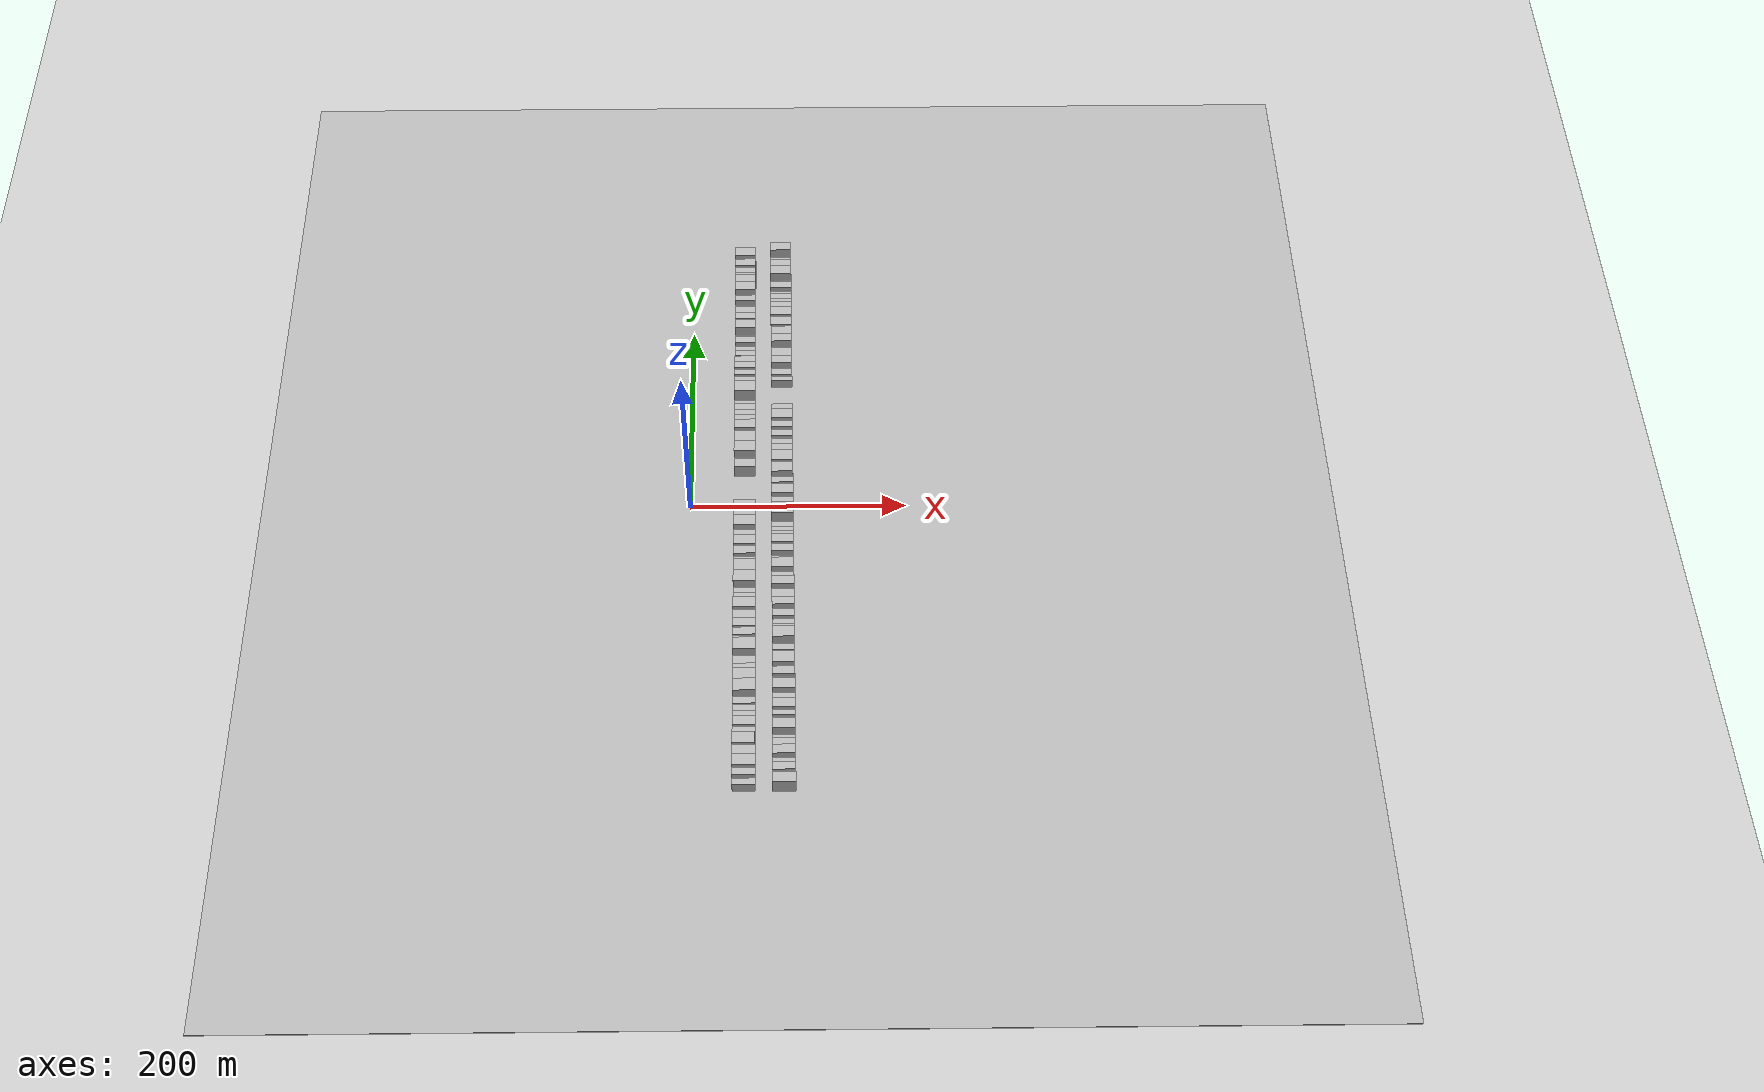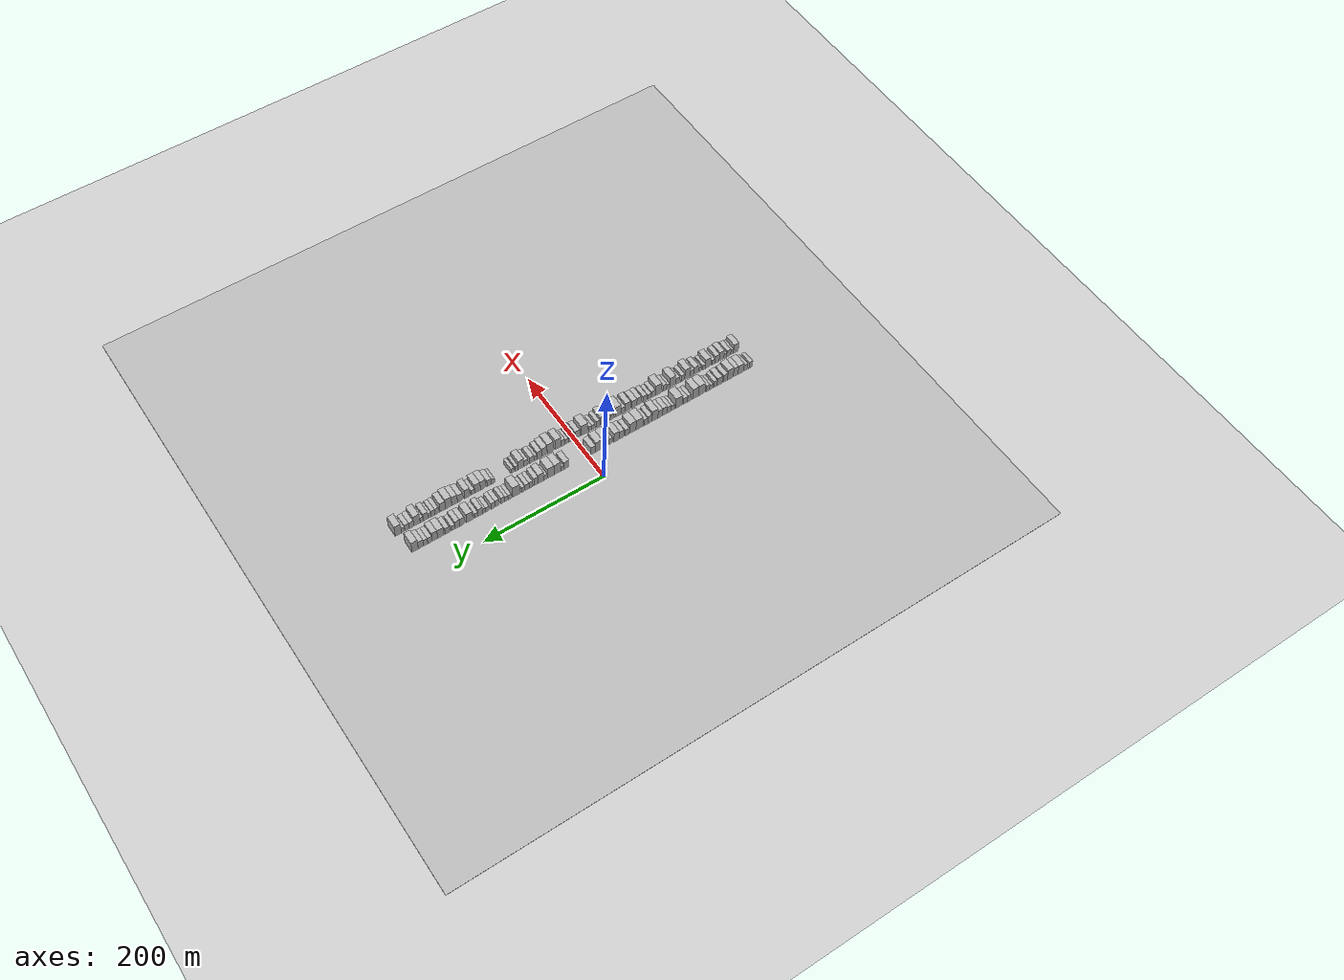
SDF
<?xml version="1.0" encoding="utf-8"?>

<sdf version="1.6">

   <world name="default">

      <gui fullscreen="0">

         <camera name="user_camera">

            <pose>-15 0 4.57585 0 0 0</pose>

            <view_controller>orbit</view_controller>

         </camera>

      </gui>

      <scene>

         <sky>

           <clouds>

             <speed>12</speed>

           </clouds>

         </sky>

         <ambient>0.4 0.4 0.4 1</ambient>

         <background>0.7 0.7 0.7 1</background>

         <shadows>1</shadows>

      </scene>

      <gravity>0 0 -9.8066</gravity>

      <magnetic_field>6e-06 2.3e-05 -4.2e-05</magnetic_field>

      <physics default="0" name="default_physics" type="ode">

         <ode>

            <solver>

               <type>quick</type>

               <iters>10</iters>

               <sor>1.0</sor>

               <use_dynamic_moi_rescaling>0</use_dynamic_moi_rescaling>

            </solver>

            <constraints>

               <cfm>0</cfm>

               <erp>0.2</erp>

               <contact_max_correcting_vel>100</contact_max_correcting_vel>

               <contact_surface_layer>0.001</contact_surface_layer>

            </constraints>

         </ode>

         <max_step_size>0.004</max_step_size>

         <real_time_factor>1</real_time_factor>

         <real_time_update_rate>250</real_time_update_rate>

      </physics>

      <light name="sun" type="directional">

         <cast_shadows>1</cast_shadows>

         <pose>0 0 10 0 0 0</pose>

         <diffuse>0.8 0.8 0.8 1</diffuse>

         <specular>0.2 0.2 0.2 1</specular>

         <attenuation>

            <range>1000</range>

            <constant>0.9</constant>

            <linear>0.01</linear>

            <quadratic>0.001</quadratic>

         </attenuation>

         <direction>-0.5 0.1 -0.9</direction>

      </light>

      <include>

         <name>ground_plane_1</name>

         <uri>model://HANNAS_ground_plane</uri>

         <pose>0 0 0  0 0 0</pose>

      </include>

      <include>

         <name>ground_plane_2</name>

         <uri>model://HANNAS_ground_plane</uri>

         <pose>100 0 0  0 0 0</pose>

      </include>

      <model name="building_1">

         <static>1</static>

         <pose frame="">50.0000 -286.9867 0 0.000000 0.000000 0.000000</pose>

         <link name="link">

            <pose frame="">0 0 7.50 0 0 0</pose>

            <collision name="collision">

               <geometry>

                  <box>

                     <size>20.0000 6.0265 15.0000</size>

                  </box>

               </geometry>

               <max_contacts>10</max_contacts>

               <surface>

                  <contact>

                     <ode/>

                  </contact>

                  <bounce/>

                  <friction>

                     <torsional>

                        <ode/>

                     </torsional>

                     <ode/>

                  </friction>

               </surface>

            </collision>

            <visual name="visual">

               <cast_shadows>0</cast_shadows>

               <geometry>

                  <box>

                     <size>20.0000 6.0265 15.0000</size>

                  </box>

               </geometry>

               <material>

                  <script>

                     <uri>model://HANNAS_wall/materials/scripts</uri>

                     <uri>model://HANNAS_wall/materials/textures</uri>

                     <name>vrc/HANNAS_wall</name>

                  </script>

               </material>

            </visual>

            <self_collide>0</self_collide>

            <enable_wind>0</enable_wind>

            <kinematic>0</kinematic>

         </link>

      </model>

      <model name="building_2">

         <static>1</static>

         <pose frame="">50.0000 -277.4261 0 0.000000 0.000000 0.000000</pose>

         <link name="link">

            <pose frame="">0 0 7.50 0 0 0</pose>

            <collision name="collision">

               <geometry>

                  <box>

                     <size>20.0000 7.0948 15.0000</size>

                  </box>

               </geometry>

               <max_contacts>10</max_contacts>

               <surface>

                  <contact>

                     <ode/>

                  </contact>

                  <bounce/>

                  <friction>

                     <torsional>

                        <ode/>

                     </torsional>

                     <ode/>

                  </friction>

               </surface>

            </collision>

            <visual name="visual">

               <cast_shadows>0</cast_shadows>

               <geometry>

                  <box>

                     <size>20.0000 7.0948 15.0000</size>

                  </box>

               </geometry>

               <material>

                  <script>

                     <uri>model://HANNAS_wall/materials/scripts</uri>

                     <uri>model://HANNAS_wall/materials/textures</uri>

                     <name>vrc/HANNAS_wall</name>

                  </script>

               </material>

            </visual>

            <self_collide>0</self_collide>

            <enable_wind>0</enable_wind>

            <kinematic>0</kinematic>

         </link>

      </model>

      <model name="building_3">

         <static>1</static>

         <pose frame="">50.0000 -268.8254 0 0.000000 0.000000 0.000000</pose>

         <link name="link">

            <pose frame="">0 0 10.50 0 0 0</pose>

            <collision name="collision">

               <geometry>

                  <box>

                     <size>20.0000 10.1066 21.0000</size>

                  </box>

               </geometry>

               <max_contacts>10</max_contacts>

               <surface>

                  <contact>

                     <ode/>

                  </contact>

                  <bounce/>

                  <friction>

                     <torsional>

                        <ode/>

                     </torsional>

                     <ode/>

                  </friction>

               </surface>

            </collision>

            <visual name="visual">

               <cast_shadows>0</cast_shadows>

               <geometry>

                  <box>

                     <size>20.0000 10.1066 21.0000</size>

                  </box>

               </geometry>

               <material>

                  <script>

                     <uri>model://HANNAS_wall/materials/scripts</uri>

                     <uri>model://HANNAS_wall/materials/textures</uri>

                     <name>vrc/HANNAS_wall</name>

                  </script>

               </material>

            </visual>

            <self_collide>0</self_collide>

            <enable_wind>0</enable_wind>

            <kinematic>0</kinematic>

         </link>

      </model>

      <model name="building_4">

         <static>1</static>

         <pose frame="">50.0000 -259.3988 0 0.000000 0.000000 0.000000</pose>

         <link name="link">

            <pose frame="">0 0 10.50 0 0 0</pose>

            <collision name="collision">

               <geometry>

                  <box>

                     <size>20.0000 8.7465 21.0000</size>

                  </box>

               </geometry>

               <max_contacts>10</max_contacts>

               <surface>

                  <contact>

                     <ode/>

                  </contact>

                  <bounce/>

                  <friction>

                     <torsional>

                        <ode/>

                     </torsional>

                     <ode/>

                  </friction>

               </surface>

            </collision>

            <visual name="visual">

               <cast_shadows>0</cast_shadows>

               <geometry>

                  <box>

                     <size>20.0000 8.7465 21.0000</size>

                  </box>

               </geometry>

               <material>

                  <script>

                     <uri>model://HANNAS_wall/materials/scripts</uri>

                     <uri>model://HANNAS_wall/materials/textures</uri>

                     <name>vrc/HANNAS_wall</name>

                  </script>

               </material>

            </visual>

            <self_collide>0</self_collide>

            <enable_wind>0</enable_wind>

            <kinematic>0</kinematic>

         </link>

      </model>

      <model name="building_5">

         <static>1</static>

         <pose frame="">50.0000 -249.8142 0 0.000000 0.000000 0.000000</pose>

         <link name="link">

            <pose frame="">0 0 12.00 0 0 0</pose>

            <collision name="collision">

               <geometry>

                  <box>

                     <size>20.0000 10.4228 24.0000</size>

                  </box>

               </geometry>

               <max_contacts>10</max_contacts>

               <surface>

                  <contact>

                     <ode/>

                  </contact>

                  <bounce/>

                  <friction>

                     <torsional>

                        <ode/>

                     </torsional>

                     <ode/>

                  </friction>

               </surface>

            </collision>

            <visual name="visual">

               <cast_shadows>0</cast_shadows>

               <geometry>

                  <box>

                     <size>20.0000 10.4228 24.0000</size>

                  </box>

               </geometry>

               <material>

                  <script>

                     <uri>model://HANNAS_wall/materials/scripts</uri>

                     <uri>model://HANNAS_wall/materials/textures</uri>

                     <name>vrc/HANNAS_wall</name>

                  </script>

               </material>

            </visual>

            <self_collide>0</self_collide>

            <enable_wind>0</enable_wind>

            <kinematic>0</kinematic>

         </link>

      </model>

      <model name="building_6">

         <static>1</static>

         <pose frame="">50.0000 -240.6786 0 0.000000 0.000000 0.000000</pose>

         <link name="link">

            <pose frame="">0 0 9.00 0 0 0</pose>

            <collision name="collision">

               <geometry>

                  <box>

                     <size>20.0000 7.8482 18.0000</size>

                  </box>

               </geometry>

               <max_contacts>10</max_contacts>

               <surface>

                  <contact>

                     <ode/>

                  </contact>

                  <bounce/>

                  <friction>

                     <torsional>

                        <ode/>

                     </torsional>

                     <ode/>

                  </friction>

               </surface>

            </collision>

            <visual name="visual">

               <cast_shadows>0</cast_shadows>

               <geometry>

                  <box>

                     <size>20.0000 7.8482 18.0000</size>

                  </box>

               </geometry>

               <material>

                  <script>

                     <uri>model://HANNAS_wall/materials/scripts</uri>

                     <uri>model://HANNAS_wall/materials/textures</uri>

                     <name>vrc/HANNAS_wall</name>

                  </script>

               </material>

            </visual>

            <self_collide>0</self_collide>

            <enable_wind>0</enable_wind>

            <kinematic>0</kinematic>

         </link>

      </model>

      <model name="building_7">

         <static>1</static>

         <pose frame="">50.0000 -230.2864 0 0.000000 0.000000 0.000000</pose>

         <link name="link">

            <pose frame="">0 0 9.00 0 0 0</pose>

            <collision name="collision">

               <geometry>

                  <box>

                     <size>20.0000 8.9361 18.0000</size>

                  </box>

               </geometry>

               <max_contacts>10</max_contacts>

               <surface>

                  <contact>

                     <ode/>

                  </contact>

                  <bounce/>

                  <friction>

                     <torsional>

                        <ode/>

                     </torsional>

                     <ode/>

                  </friction>

               </surface>

            </collision>

            <visual name="visual">

               <cast_shadows>0</cast_shadows>

               <geometry>

                  <box>

                     <size>20.0000 8.9361 18.0000</size>

                  </box>

               </geometry>

               <material>

                  <script>

                     <uri>model://HANNAS_wall/materials/scripts</uri>

                     <uri>model://HANNAS_wall/materials/textures</uri>

                     <name>vrc/HANNAS_wall</name>

                  </script>

               </material>

            </visual>

            <self_collide>0</self_collide>

            <enable_wind>0</enable_wind>

            <kinematic>0</kinematic>

         </link>

      </model>

      <model name="building_8">

         <static>1</static>

         <pose frame="">50.0000 -222.8066 0 0.000000 0.000000 0.000000</pose>

         <link name="link">

            <pose frame="">0 0 7.50 0 0 0</pose>

            <collision name="collision">

               <geometry>

                  <box>

                     <size>20.0000 6.0235 15.0000</size>

                  </box>

               </geometry>

               <max_contacts>10</max_contacts>

               <surface>

                  <contact>

                     <ode/>

                  </contact>

                  <bounce/>

                  <friction>

                     <torsional>

                        <ode/>

                     </torsional>

                     <ode/>

                  </friction>

               </surface>

            </collision>

            <visual name="visual">

               <cast_shadows>0</cast_shadows>

               <geometry>

                  <box>

                     <size>20.0000 6.0235 15.0000</size>

                  </box>

               </geometry>

               <material>

                  <script>

                     <uri>model://HANNAS_wall/materials/scripts</uri>

                     <uri>model://HANNAS_wall/materials/textures</uri>

                     <name>vrc/HANNAS_wall</name>

                  </script>

               </material>

            </visual>

            <self_collide>0</self_collide>

            <enable_wind>0</enable_wind>

            <kinematic>0</kinematic>

         </link>

      </model>

      <model name="building_9">

         <static>1</static>

         <pose frame="">50.0000 -215.0221 0 0.000000 0.000000 0.000000</pose>

         <link name="link">

            <pose frame="">0 0 6.00 0 0 0</pose>

            <collision name="collision">

               <geometry>

                  <box>

                     <size>20.0000 5.5455 12.0000</size>

                  </box>

               </geometry>

               <max_contacts>10</max_contacts>

               <surface>

                  <contact>

                     <ode/>

                  </contact>

                  <bounce/>

                  <friction>

                     <torsional>

                        <ode/>

                     </torsional>

                     <ode/>

                  </friction>

               </surface>

            </collision>

            <visual name="visual">

               <cast_shadows>0</cast_shadows>

               <geometry>

                  <box>

                     <size>20.0000 5.5455 12.0000</size>

                  </box>

               </geometry>

               <material>

                  <script>

                     <uri>model://HANNAS_wall/materials/scripts</uri>

                     <uri>model://HANNAS_wall/materials/textures</uri>

                     <name>vrc/HANNAS_wall</name>

                  </script>

               </material>

            </visual>

            <self_collide>0</self_collide>

            <enable_wind>0</enable_wind>

            <kinematic>0</kinematic>

         </link>

      </model>

      <model name="building_10">

         <static>1</static>

         <pose frame="">50.0000 -209.1622 0 0.000000 0.000000 0.000000</pose>

         <link name="link">

            <pose frame="">0 0 7.50 0 0 0</pose>

            <collision name="collision">

               <geometry>

                  <box>

                     <size>20.0000 6.1743 15.0000</size>

                  </box>

               </geometry>

               <max_contacts>10</max_contacts>

               <surface>

                  <contact>

                     <ode/>

                  </contact>

                  <bounce/>

                  <friction>

                     <torsional>

                        <ode/>

                     </torsional>

                     <ode/>

                  </friction>

               </surface>

            </collision>

            <visual name="visual">

               <cast_shadows>0</cast_shadows>

               <geometry>

                  <box>

                     <size>20.0000 6.1743 15.0000</size>

                  </box>

               </geometry>

               <material>

                  <script>

                     <uri>model://HANNAS_wall/materials/scripts</uri>

                     <uri>model://HANNAS_wall/materials/textures</uri>

                     <name>vrc/HANNAS_wall</name>

                  </script>

               </material>

            </visual>

            <self_collide>0</self_collide>

            <enable_wind>0</enable_wind>

            <kinematic>0</kinematic>

         </link>

      </model>

      <model name="building_11">

         <static>1</static>

         <pose frame="">50.0000 -198.1938 0 0.000000 0.000000 0.000000</pose>

         <link name="link">

            <pose frame="">0 0 12.00 0 0 0</pose>

            <collision name="collision">

               <geometry>

                  <box>

                     <size>20.0000 11.7625 24.0000</size>

                  </box>

               </geometry>

               <max_contacts>10</max_contacts>

               <surface>

                  <contact>

                     <ode/>

                  </contact>

                  <bounce/>

                  <friction>

                     <torsional>

                        <ode/>

                     </torsional>

                     <ode/>

                  </friction>

               </surface>

            </collision>

            <visual name="visual">

               <cast_shadows>0</cast_shadows>

               <geometry>

                  <box>

                     <size>20.0000 11.7625 24.0000</size>

                  </box>

               </geometry>

               <material>

                  <script>

                     <uri>model://HANNAS_wall/materials/scripts</uri>

                     <uri>model://HANNAS_wall/materials/textures</uri>

                     <name>vrc/HANNAS_wall</name>

                  </script>

               </material>

            </visual>

            <self_collide>0</self_collide>

            <enable_wind>0</enable_wind>

            <kinematic>0</kinematic>

         </link>

      </model>

      <model name="building_12">

         <static>1</static>

         <pose frame="">50.0000 -187.0191 0 0.000000 0.000000 0.000000</pose>

         <link name="link">

            <pose frame="">0 0 12.00 0 0 0</pose>

            <collision name="collision">

               <geometry>

                  <box>

                     <size>20.0000 10.5870 24.0000</size>

                  </box>

               </geometry>

               <max_contacts>10</max_contacts>

               <surface>

                  <contact>

                     <ode/>

                  </contact>

                  <bounce/>

                  <friction>

                     <torsional>

                        <ode/>

                     </torsional>

                     <ode/>

                  </friction>

               </surface>

            </collision>

            <visual name="visual">

               <cast_shadows>0</cast_shadows>

               <geometry>

                  <box>

                     <size>20.0000 10.5870 24.0000</size>

                  </box>

               </geometry>

               <material>

                  <script>

                     <uri>model://HANNAS_wall/materials/scripts</uri>

                     <uri>model://HANNAS_wall/materials/textures</uri>

                     <name>vrc/HANNAS_wall</name>

                  </script>

               </material>

            </visual>

            <self_collide>0</self_collide>

            <enable_wind>0</enable_wind>

            <kinematic>0</kinematic>

         </link>

      </model>

      <model name="building_13">

         <static>1</static>

         <pose frame="">50.0000 -175.7036 0 0.000000 0.000000 0.000000</pose>

         <link name="link">

            <pose frame="">0 0 7.50 0 0 0</pose>

            <collision name="collision">

               <geometry>

                  <box>

                     <size>20.0000 6.0440 15.0000</size>

                  </box>

               </geometry>

               <max_contacts>10</max_contacts>

               <surface>

                  <contact>

                     <ode/>

                  </contact>

                  <bounce/>

                  <friction>

                     <torsional>

                        <ode/>

                     </torsional>

                     <ode/>

                  </friction>

               </surface>

            </collision>

            <visual name="visual">

               <cast_shadows>0</cast_shadows>

               <geometry>

                  <box>

                     <size>20.0000 6.0440 15.0000</size>

                  </box>

               </geometry>

               <material>

                  <script>

                     <uri>model://HANNAS_wall/materials/scripts</uri>

                     <uri>model://HANNAS_wall/materials/textures</uri>

                     <name>vrc/HANNAS_wall</name>

                  </script>

               </material>

            </visual>

            <self_collide>0</self_collide>

            <enable_wind>0</enable_wind>

            <kinematic>0</kinematic>

         </link>

      </model>

      <model name="building_14">

         <static>1</static>

         <pose frame="">50.0000 -169.0348 0 0.000000 0.000000 0.000000</pose>

         <link name="link">

            <pose frame="">0 0 7.50 0 0 0</pose>

            <collision name="collision">

               <geometry>

                  <box>

                     <size>20.0000 7.2937 15.0000</size>

                  </box>

               </geometry>

               <max_contacts>10</max_contacts>

               <surface>

                  <contact>

                     <ode/>

                  </contact>

                  <bounce/>

                  <friction>

                     <torsional>

                        <ode/>

                     </torsional>

                     <ode/>

                  </friction>

               </surface>

            </collision>

            <visual name="visual">

               <cast_shadows>0</cast_shadows>

               <geometry>

                  <box>

                     <size>20.0000 7.2937 15.0000</size>

                  </box>

               </geometry>

               <material>

                  <script>

                     <uri>model://HANNAS_wall/materials/scripts</uri>

                     <uri>model://HANNAS_wall/materials/textures</uri>

                     <name>vrc/HANNAS_wall</name>

                  </script>

               </material>

            </visual>

            <self_collide>0</self_collide>

            <enable_wind>0</enable_wind>

            <kinematic>0</kinematic>

         </link>

      </model>

      <model name="building_15">

         <static>1</static>

         <pose frame="">50.0000 -157.3991 0 0.000000 0.000000 0.000000</pose>

         <link name="link">

            <pose frame="">0 0 12.00 0 0 0</pose>

            <collision name="collision">

               <geometry>

                  <box>

                     <size>20.0000 11.9776 24.0000</size>

                  </box>

               </geometry>

               <max_contacts>10</max_contacts>

               <surface>

                  <contact>

                     <ode/>

                  </contact>

                  <bounce/>

                  <friction>

                     <torsional>

                        <ode/>

                     </torsional>

                     <ode/>

                  </friction>

               </surface>

            </collision>

            <visual name="visual">

               <cast_shadows>0</cast_shadows>

               <geometry>

                  <box>

                     <size>20.0000 11.9776 24.0000</size>

                  </box>

               </geometry>

               <material>

                  <script>

                     <uri>model://HANNAS_wall/materials/scripts</uri>

                     <uri>model://HANNAS_wall/materials/textures</uri>

                     <name>vrc/HANNAS_wall</name>

                  </script>

               </material>

            </visual>

            <self_collide>0</self_collide>

            <enable_wind>0</enable_wind>

            <kinematic>0</kinematic>

         </link>

      </model>

      <model name="building_16">

         <static>1</static>

         <pose frame="">50.0000 -146.4578 0 0.000000 0.000000 0.000000</pose>

         <link name="link">

            <pose frame="">0 0 6.00 0 0 0</pose>

            <collision name="collision">

               <geometry>

                  <box>

                     <size>20.0000 5.9051 12.0000</size>

                  </box>

               </geometry>

               <max_contacts>10</max_contacts>

               <surface>

                  <contact>

                     <ode/>

                  </contact>

                  <bounce/>

                  <friction>

                     <torsional>

                        <ode/>

                     </torsional>

                     <ode/>

                  </friction>

               </surface>

            </collision>

            <visual name="visual">

               <cast_shadows>0</cast_shadows>

               <geometry>

                  <box>

                     <size>20.0000 5.9051 12.0000</size>

                  </box>

               </geometry>

               <material>

                  <script>

                     <uri>model://HANNAS_wall/materials/scripts</uri>

                     <uri>model://HANNAS_wall/materials/textures</uri>

                     <name>vrc/HANNAS_wall</name>

                  </script>

               </material>

            </visual>

            <self_collide>0</self_collide>

            <enable_wind>0</enable_wind>

            <kinematic>0</kinematic>

         </link>

      </model>

      <model name="building_17">

         <static>1</static>

         <pose frame="">50.0000 -139.8941 0 0.000000 0.000000 0.000000</pose>

         <link name="link">

            <pose frame="">0 0 7.50 0 0 0</pose>

            <collision name="collision">

               <geometry>

                  <box>

                     <size>20.0000 7.2222 15.0000</size>

                  </box>

               </geometry>

               <max_contacts>10</max_contacts>

               <surface>

                  <contact>

                     <ode/>

                  </contact>

                  <bounce/>

                  <friction>

                     <torsional>

                        <ode/>

                     </torsional>

                     <ode/>

                  </friction>

               </surface>

            </collision>

            <visual name="visual">

               <cast_shadows>0</cast_shadows>

               <geometry>

                  <box>

                     <size>20.0000 7.2222 15.0000</size>

                  </box>

               </geometry>

               <material>

                  <script>

                     <uri>model://HANNAS_wall/materials/scripts</uri>

                     <uri>model://HANNAS_wall/materials/textures</uri>

                     <name>vrc/HANNAS_wall</name>

                  </script>

               </material>

            </visual>

            <self_collide>0</self_collide>

            <enable_wind>0</enable_wind>

            <kinematic>0</kinematic>

         </link>

      </model>

      <model name="building_18">

         <static>1</static>

         <pose frame="">50.0000 -132.3141 0 0.000000 0.000000 0.000000</pose>

         <link name="link">

            <pose frame="">0 0 9.00 0 0 0</pose>

            <collision name="collision">

               <geometry>

                  <box>

                     <size>20.0000 7.9379 18.0000</size>

                  </box>

               </geometry>

               <max_contacts>10</max_contacts>

               <surface>

                  <contact>

                     <ode/>

                  </contact>

                  <bounce/>

                  <friction>

                     <torsional>

                        <ode/>

                     </torsional>

                     <ode/>

                  </friction>

               </surface>

            </collision>

            <visual name="visual">

               <cast_shadows>0</cast_shadows>

               <geometry>

                  <box>

                     <size>20.0000 7.9379 18.0000</size>

                  </box>

               </geometry>

               <material>

                  <script>

                     <uri>model://HANNAS_wall/materials/scripts</uri>

                     <uri>model://HANNAS_wall/materials/textures</uri>

                     <name>vrc/HANNAS_wall</name>

                  </script>

               </material>

            </visual>

            <self_collide>0</self_collide>

            <enable_wind>0</enable_wind>

            <kinematic>0</kinematic>

         </link>

      </model>

      <model name="building_19">

         <static>1</static>

         <pose frame="">50.0000 -124.2348 0 0.000000 0.000000 0.000000</pose>

         <link name="link">

            <pose frame="">0 0 9.00 0 0 0</pose>

            <collision name="collision">

               <geometry>

                  <box>

                     <size>20.0000 8.2207 18.0000</size>

                  </box>

               </geometry>

               <max_contacts>10</max_contacts>

               <surface>

                  <contact>

                     <ode/>

                  </contact>

                  <bounce/>

                  <friction>

                     <torsional>

                        <ode/>

                     </torsional>

                     <ode/>

                  </friction>

               </surface>

            </collision>

            <visual name="visual">

               <cast_shadows>0</cast_shadows>

               <geometry>

                  <box>

                     <size>20.0000 8.2207 18.0000</size>

                  </box>

               </geometry>

               <material>

                  <script>

                     <uri>model://HANNAS_wall/materials/scripts</uri>

                     <uri>model://HANNAS_wall/materials/textures</uri>

                     <name>vrc/HANNAS_wall</name>

                  </script>

               </material>

            </visual>

            <self_collide>0</self_collide>

            <enable_wind>0</enable_wind>

            <kinematic>0</kinematic>

         </link>

      </model>

      <model name="building_20">

         <static>1</static>

         <pose frame="">50.0000 -114.9453 0 0.000000 0.000000 0.000000</pose>

         <link name="link">

            <pose frame="">0 0 12.00 0 0 0</pose>

            <collision name="collision">

               <geometry>

                  <box>

                     <size>20.0000 10.3582 24.0000</size>

                  </box>

               </geometry>

               <max_contacts>10</max_contacts>

               <surface>

                  <contact>

                     <ode/>

                  </contact>

                  <bounce/>

                  <friction>

                     <torsional>

                        <ode/>

                     </torsional>

                     <ode/>

                  </friction>

               </surface>

            </collision>

            <visual name="visual">

               <cast_shadows>0</cast_shadows>

               <geometry>

                  <box>

                     <size>20.0000 10.3582 24.0000</size>

                  </box>

               </geometry>

               <material>

                  <script>

                     <uri>model://HANNAS_wall/materials/scripts</uri>

                     <uri>model://HANNAS_wall/materials/textures</uri>

                     <name>vrc/HANNAS_wall</name>

                  </script>

               </material>

            </visual>

            <self_collide>0</self_collide>

            <enable_wind>0</enable_wind>

            <kinematic>0</kinematic>

         </link>

      </model>

      <model name="building_21">

         <static>1</static>

         <pose frame="">50.0000 -105.9555 0 0.000000 0.000000 0.000000</pose>

         <link name="link">

            <pose frame="">0 0 9.00 0 0 0</pose>

            <collision name="collision">

               <geometry>

                  <box>

                     <size>20.0000 7.6214 18.0000</size>

                  </box>

               </geometry>

               <max_contacts>10</max_contacts>

               <surface>

                  <contact>

                     <ode/>

                  </contact>

                  <bounce/>

                  <friction>

                     <torsional>

                        <ode/>

                     </torsional>

                     <ode/>

                  </friction>

               </surface>

            </collision>

            <visual name="visual">

               <cast_shadows>0</cast_shadows>

               <geometry>

                  <box>

                     <size>20.0000 7.6214 18.0000</size>

                  </box>

               </geometry>

               <material>

                  <script>

                     <uri>model://HANNAS_wall/materials/scripts</uri>

                     <uri>model://HANNAS_wall/materials/textures</uri>

                     <name>vrc/HANNAS_wall</name>

                  </script>

               </material>

            </visual>

            <self_collide>0</self_collide>

            <enable_wind>0</enable_wind>

            <kinematic>0</kinematic>

         </link>

      </model>

      <model name="building_22">

         <static>1</static>

         <pose frame="">50.0000 -98.8913 0 0.000000 0.000000 0.000000</pose>

         <link name="link">

            <pose frame="">0 0 7.50 0 0 0</pose>

            <collision name="collision">

               <geometry>

                  <box>

                     <size>20.0000 6.5070 15.0000</size>

                  </box>

               </geometry>

               <max_contacts>10</max_contacts>

               <surface>

                  <contact>

                     <ode/>

                  </contact>

                  <bounce/>

                  <friction>

                     <torsional>

                        <ode/>

                     </torsional>

                     <ode/>

                  </friction>

               </surface>

            </collision>

            <visual name="visual">

               <cast_shadows>0</cast_shadows>

               <geometry>

                  <box>

                     <size>20.0000 6.5070 15.0000</size>

                  </box>

               </geometry>

               <material>

                  <script>

                     <uri>model://HANNAS_wall/materials/scripts</uri>

                     <uri>model://HANNAS_wall/materials/textures</uri>

                     <name>vrc/HANNAS_wall</name>

                  </script>

               </material>

            </visual>

            <self_collide>0</self_collide>

            <enable_wind>0</enable_wind>

            <kinematic>0</kinematic>

         </link>

      </model>

      <model name="building_23">

         <static>1</static>

         <pose frame="">50.0000 -87.6615 0 0.000000 0.000000 0.000000</pose>

         <link name="link">

            <pose frame="">0 0 12.00 0 0 0</pose>

            <collision name="collision">

               <geometry>

                  <box>

                     <size>20.0000 11.9526 24.0000</size>

                  </box>

               </geometry>

               <max_contacts>10</max_contacts>

               <surface>

                  <contact>

                     <ode/>

                  </contact>

                  <bounce/>

                  <friction>

                     <torsional>

                        <ode/>

                     </torsional>

                     <ode/>

                  </friction>

               </surface>

            </collision>

            <visual name="visual">

               <cast_shadows>0</cast_shadows>

               <geometry>

                  <box>

                     <size>20.0000 11.9526 24.0000</size>

                  </box>

               </geometry>

               <material>

                  <script>

                     <uri>model://HANNAS_wall/materials/scripts</uri>

                     <uri>model://HANNAS_wall/materials/textures</uri>

                     <name>vrc/HANNAS_wall</name>

                  </script>

               </material>

            </visual>

            <self_collide>0</self_collide>

            <enable_wind>0</enable_wind>

            <kinematic>0</kinematic>

         </link>

      </model>

      <model name="building_24">

         <static>1</static>

         <pose frame="">50.0000 -75.9016 0 0.000000 0.000000 0.000000</pose>

         <link name="link">

            <pose frame="">0 0 12.00 0 0 0</pose>

            <collision name="collision">

               <geometry>

                  <box>

                     <size>20.0000 11.5673 24.0000</size>

                  </box>

               </geometry>

               <max_contacts>10</max_contacts>

               <surface>

                  <contact>

                     <ode/>

                  </contact>

                  <bounce/>

                  <friction>

                     <torsional>

                        <ode/>

                     </torsional>

                     <ode/>

                  </friction>

               </surface>

            </collision>

            <visual name="visual">

               <cast_shadows>0</cast_shadows>

               <geometry>

                  <box>

                     <size>20.0000 11.5673 24.0000</size>

                  </box>

               </geometry>

               <material>

                  <script>

                     <uri>model://HANNAS_wall/materials/scripts</uri>

                     <uri>model://HANNAS_wall/materials/textures</uri>

                     <name>vrc/HANNAS_wall</name>

                  </script>

               </material>

            </visual>

            <self_collide>0</self_collide>

            <enable_wind>0</enable_wind>

            <kinematic>0</kinematic>

         </link>

      </model>

      <model name="building_25">

         <static>1</static>

         <pose frame="">50.0000 -66.5488 0 0.000000 0.000000 0.000000</pose>

         <link name="link">

            <pose frame="">0 0 7.50 0 0 0</pose>

            <collision name="collision">

               <geometry>

                  <box>

                     <size>20.0000 7.1383 15.0000</size>

                  </box>

               </geometry>

               <max_contacts>10</max_contacts>

               <surface>

                  <contact>

                     <ode/>

                  </contact>

                  <bounce/>

                  <friction>

                     <torsional>

                        <ode/>

                     </torsional>

                     <ode/>

                  </friction>

               </surface>

            </collision>

            <visual name="visual">

               <cast_shadows>0</cast_shadows>

               <geometry>

                  <box>

                     <size>20.0000 7.1383 15.0000</size>

                  </box>

               </geometry>

               <material>

                  <script>

                     <uri>model://HANNAS_wall/materials/scripts</uri>

                     <uri>model://HANNAS_wall/materials/textures</uri>

                     <name>vrc/HANNAS_wall</name>

                  </script>

               </material>

            </visual>

            <self_collide>0</self_collide>

            <enable_wind>0</enable_wind>

            <kinematic>0</kinematic>

         </link>

      </model>

      <model name="building_26">

         <static>1</static>

         <pose frame="">50.0000 -56.9321 0 0.000000 0.000000 0.000000</pose>

         <link name="link">

            <pose frame="">0 0 9.00 0 0 0</pose>

            <collision name="collision">

               <geometry>

                  <box>

                     <size>20.0000 8.0951 18.0000</size>

                  </box>

               </geometry>

               <max_contacts>10</max_contacts>

               <surface>

                  <contact>

                     <ode/>

                  </contact>

                  <bounce/>

                  <friction>

                     <torsional>

                        <ode/>

                     </torsional>

                     <ode/>

                  </friction>

               </surface>

            </collision>

            <visual name="visual">

               <cast_shadows>0</cast_shadows>

               <geometry>

                  <box>

                     <size>20.0000 8.0951 18.0000</size>

                  </box>

               </geometry>

               <material>

                  <script>

                     <uri>model://HANNAS_wall/materials/scripts</uri>

                     <uri>model://HANNAS_wall/materials/textures</uri>

                     <name>vrc/HANNAS_wall</name>

                  </script>

               </material>

            </visual>

            <self_collide>0</self_collide>

            <enable_wind>0</enable_wind>

            <kinematic>0</kinematic>

         </link>

      </model>

      <model name="building_27">

         <static>1</static>

         <pose frame="">50.0000 -48.1220 0 0.000000 0.000000 0.000000</pose>

         <link name="link">

            <pose frame="">0 0 10.50 0 0 0</pose>

            <collision name="collision">

               <geometry>

                  <box>

                     <size>20.0000 9.5251 21.0000</size>

                  </box>

               </geometry>

               <max_contacts>10</max_contacts>

               <surface>

                  <contact>

                     <ode/>

                  </contact>

                  <bounce/>

                  <friction>

                     <torsional>

                        <ode/>

                     </torsional>

                     <ode/>

                  </friction>

               </surface>

            </collision>

            <visual name="visual">

               <cast_shadows>0</cast_shadows>

               <geometry>

                  <box>

                     <size>20.0000 9.5251 21.0000</size>

                  </box>

               </geometry>

               <material>

                  <script>

                     <uri>model://HANNAS_wall/materials/scripts</uri>

                     <uri>model://HANNAS_wall/materials/textures</uri>

                     <name>vrc/HANNAS_wall</name>

                  </script>

               </material>

            </visual>

            <self_collide>0</self_collide>

            <enable_wind>0</enable_wind>

            <kinematic>0</kinematic>

         </link>

      </model>

      <model name="building_28">

         <static>1</static>

         <pose frame="">50.0000 -37.1234 0 0.000000 0.000000 0.000000</pose>

         <link name="link">

            <pose frame="">0 0 7.50 0 0 0</pose>

            <collision name="collision">

               <geometry>

                  <box>

                     <size>20.0000 6.4721 15.0000</size>

                  </box>

               </geometry>

               <max_contacts>10</max_contacts>

               <surface>

                  <contact>

                     <ode/>

                  </contact>

                  <bounce/>

                  <friction>

                     <torsional>

                        <ode/>

                     </torsional>

                     <ode/>

                  </friction>

               </surface>

            </collision>

            <visual name="visual">

               <cast_shadows>0</cast_shadows>

               <geometry>

                  <box>

                     <size>20.0000 6.4721 15.0000</size>

                  </box>

               </geometry>

               <material>

                  <script>

                     <uri>model://HANNAS_wall/materials/scripts</uri>

                     <uri>model://HANNAS_wall/materials/textures</uri>

                     <name>vrc/HANNAS_wall</name>

                  </script>

               </material>

            </visual>

            <self_collide>0</self_collide>

            <enable_wind>0</enable_wind>

            <kinematic>0</kinematic>

         </link>

      </model>

      <model name="building_29">

         <static>1</static>

         <pose frame="">50.0000 -28.4028 0 0.000000 0.000000 0.000000</pose>

         <link name="link">

            <pose frame="">0 0 12.00 0 0 0</pose>

            <collision name="collision">

               <geometry>

                  <box>

                     <size>20.0000 10.9692 24.0000</size>

                  </box>

               </geometry>

               <max_contacts>10</max_contacts>

               <surface>

                  <contact>

                     <ode/>

                  </contact>

                  <bounce/>

                  <friction>

                     <torsional>

                        <ode/>

                     </torsional>

                     <ode/>

                  </friction>

               </surface>

            </collision>

            <visual name="visual">

               <cast_shadows>0</cast_shadows>

               <geometry>

                  <box>

                     <size>20.0000 10.9692 24.0000</size>

                  </box>

               </geometry>

               <material>

                  <script>

                     <uri>model://HANNAS_wall/materials/scripts</uri>

                     <uri>model://HANNAS_wall/materials/textures</uri>

                     <name>vrc/HANNAS_wall</name>

                  </script>

               </material>

            </visual>

            <self_collide>0</self_collide>

            <enable_wind>0</enable_wind>

            <kinematic>0</kinematic>

         </link>

      </model>

      <model name="building_30">

         <static>1</static>

         <pose frame="">50.0000 -17.3656 0 0.000000 0.000000 0.000000</pose>

         <link name="link">

            <pose frame="">0 0 12.00 0 0 0</pose>

            <collision name="collision">

               <geometry>

                  <box>

                     <size>20.0000 11.1053 24.0000</size>

                  </box>

               </geometry>

               <max_contacts>10</max_contacts>

               <surface>

                  <contact>

                     <ode/>

                  </contact>

                  <bounce/>

                  <friction>

                     <torsional>

                        <ode/>

                     </torsional>

                     <ode/>

                  </friction>

               </surface>

            </collision>

            <visual name="visual">

               <cast_shadows>0</cast_shadows>

               <geometry>

                  <box>

                     <size>20.0000 11.1053 24.0000</size>

                  </box>

               </geometry>

               <material>

                  <script>

                     <uri>model://HANNAS_wall/materials/scripts</uri>

                     <uri>model://HANNAS_wall/materials/textures</uri>

                     <name>vrc/HANNAS_wall</name>

                  </script>

               </material>

            </visual>

            <self_collide>0</self_collide>

            <enable_wind>0</enable_wind>

            <kinematic>0</kinematic>

         </link>

      </model>

      <model name="building_31">

         <static>1</static>

         <pose frame="">50.0000 -7.4308 0 0.000000 0.000000 0.000000</pose>

         <link name="link">

            <pose frame="">0 0 9.00 0 0 0</pose>

            <collision name="collision">

               <geometry>

                  <box>

                     <size>20.0000 8.7644 18.0000</size>

                  </box>

               </geometry>

               <max_contacts>10</max_contacts>

               <surface>

                  <contact>

                     <ode/>

                  </contact>

                  <bounce/>

                  <friction>

                     <torsional>

                        <ode/>

                     </torsional>

                     <ode/>

                  </friction>

               </surface>

            </collision>

            <visual name="visual">

               <cast_shadows>0</cast_shadows>

               <geometry>

                  <box>

                     <size>20.0000 8.7644 18.0000</size>

                  </box>

               </geometry>

               <material>

                  <script>

                     <uri>model://HANNAS_wall/materials/scripts</uri>

                     <uri>model://HANNAS_wall/materials/textures</uri>

                     <name>vrc/HANNAS_wall</name>

                  </script>

               </material>

            </visual>

            <self_collide>0</self_collide>

            <enable_wind>0</enable_wind>

            <kinematic>0</kinematic>

         </link>

      </model>

      <model name="building_32">

         <static>1</static>

         <pose frame="">50.0000 38.1596 0 0.000000 0.000000 0.000000</pose>

         <link name="link">

            <pose frame="">0 0 9.00 0 0 0</pose>

            <collision name="collision">

               <geometry>

                  <box>

                     <size>20.0000 8.8054 18.0000</size>

                  </box>

               </geometry>

               <max_contacts>10</max_contacts>

               <surface>

                  <contact>

                     <ode/>

                  </contact>

                  <bounce/>

                  <friction>

                     <torsional>

                        <ode/>

                     </torsional>

                     <ode/>

                  </friction>

               </surface>

            </collision>

            <visual name="visual">

               <cast_shadows>0</cast_shadows>

               <geometry>

                  <box>

                     <size>20.0000 8.8054 18.0000</size>

                  </box>

               </geometry>

               <material>

                  <script>

                     <uri>model://HANNAS_wall/materials/scripts</uri>

                     <uri>model://HANNAS_wall/materials/textures</uri>

                     <name>vrc/HANNAS_wall</name>

                  </script>

               </material>

            </visual>

            <self_collide>0</self_collide>

            <enable_wind>0</enable_wind>

            <kinematic>0</kinematic>

         </link>

      </model>

      <model name="building_33">

         <static>1</static>

         <pose frame="">50.0000 45.2010 0 0.000000 0.000000 0.000000</pose>

         <link name="link">

            <pose frame="">0 0 6.00 0 0 0</pose>

            <collision name="collision">

               <geometry>

                  <box>

                     <size>20.0000 5.2773 12.0000</size>

                  </box>

               </geometry>

               <max_contacts>10</max_contacts>

               <surface>

                  <contact>

                     <ode/>

                  </contact>

                  <bounce/>

                  <friction>

                     <torsional>

                        <ode/>

                     </torsional>

                     <ode/>

                  </friction>

               </surface>

            </collision>

            <visual name="visual">

               <cast_shadows>0</cast_shadows>

               <geometry>

                  <box>

                     <size>20.0000 5.2773 12.0000</size>

                  </box>

               </geometry>

               <material>

                  <script>

                     <uri>model://HANNAS_wall/materials/scripts</uri>

                     <uri>model://HANNAS_wall/materials/textures</uri>

                     <name>vrc/HANNAS_wall</name>

                  </script>

               </material>

            </visual>

            <self_collide>0</self_collide>

            <enable_wind>0</enable_wind>

            <kinematic>0</kinematic>

         </link>

      </model>

      <model name="building_34">

         <static>1</static>

         <pose frame="">50.0000 53.1479 0 0.000000 0.000000 0.000000</pose>

         <link name="link">

            <pose frame="">0 0 12.00 0 0 0</pose>

            <collision name="collision">

               <geometry>

                  <box>

                     <size>20.0000 10.6165 24.0000</size>

                  </box>

               </geometry>

               <max_contacts>10</max_contacts>

               <surface>

                  <contact>

                     <ode/>

                  </contact>

                  <bounce/>

                  <friction>

                     <torsional>

                        <ode/>

                     </torsional>

                     <ode/>

                  </friction>

               </surface>

            </collision>

            <visual name="visual">

               <cast_shadows>0</cast_shadows>

               <geometry>

                  <box>

                     <size>20.0000 10.6165 24.0000</size>

                  </box>

               </geometry>

               <material>

                  <script>

                     <uri>model://HANNAS_wall/materials/scripts</uri>

                     <uri>model://HANNAS_wall/materials/textures</uri>

                     <name>vrc/HANNAS_wall</name>

                  </script>

               </material>

            </visual>

            <self_collide>0</self_collide>

            <enable_wind>0</enable_wind>

            <kinematic>0</kinematic>

         </link>

      </model>

      <model name="building_35">

         <static>1</static>

         <pose frame="">50.0000 64.3146 0 0.000000 0.000000 0.000000</pose>

         <link name="link">

            <pose frame="">0 0 12.00 0 0 0</pose>

            <collision name="collision">

               <geometry>

                  <box>

                     <size>20.0000 11.7168 24.0000</size>

                  </box>

               </geometry>

               <max_contacts>10</max_contacts>

               <surface>

                  <contact>

                     <ode/>

                  </contact>

                  <bounce/>

                  <friction>

                     <torsional>

                        <ode/>

                     </torsional>

                     <ode/>

                  </friction>

               </surface>

            </collision>

            <visual name="visual">

               <cast_shadows>0</cast_shadows>

               <geometry>

                  <box>

                     <size>20.0000 11.7168 24.0000</size>

                  </box>

               </geometry>

               <material>

                  <script>

                     <uri>model://HANNAS_wall/materials/scripts</uri>

                     <uri>model://HANNAS_wall/materials/textures</uri>

                     <name>vrc/HANNAS_wall</name>

                  </script>

               </material>

            </visual>

            <self_collide>0</self_collide>

            <enable_wind>0</enable_wind>

            <kinematic>0</kinematic>

         </link>

      </model>

      <model name="building_36">

         <static>1</static>

         <pose frame="">50.0000 73.0456 0 0.000000 0.000000 0.000000</pose>

         <link name="link">

            <pose frame="">0 0 6.00 0 0 0</pose>

            <collision name="collision">

               <geometry>

                  <box>

                     <size>20.0000 5.7453 12.0000</size>

                  </box>

               </geometry>

               <max_contacts>10</max_contacts>

               <surface>

                  <contact>

                     <ode/>

                  </contact>

                  <bounce/>

                  <friction>

                     <torsional>

                        <ode/>

                     </torsional>

                     <ode/>

                  </friction>

               </surface>

            </collision>

            <visual name="visual">

               <cast_shadows>0</cast_shadows>

               <geometry>

                  <box>

                     <size>20.0000 5.7453 12.0000</size>

                  </box>

               </geometry>

               <material>

                  <script>

                     <uri>model://HANNAS_wall/materials/scripts</uri>

                     <uri>model://HANNAS_wall/materials/textures</uri>

                     <name>vrc/HANNAS_wall</name>

                  </script>

               </material>

            </visual>

            <self_collide>0</self_collide>

            <enable_wind>0</enable_wind>

            <kinematic>0</kinematic>

         </link>

      </model>

      <model name="building_37">

         <static>1</static>

         <pose frame="">50.0000 80.6158 0 0.000000 0.000000 0.000000</pose>

         <link name="link">

            <pose frame="">0 0 10.50 0 0 0</pose>

            <collision name="collision">

               <geometry>

                  <box>

                     <size>20.0000 9.3951 21.0000</size>

                  </box>

               </geometry>

               <max_contacts>10</max_contacts>

               <surface>

                  <contact>

                     <ode/>

                  </contact>

                  <bounce/>

                  <friction>

                     <torsional>

                        <ode/>

                     </torsional>

                     <ode/>

                  </friction>

               </surface>

            </collision>

            <visual name="visual">

               <cast_shadows>0</cast_shadows>

               <geometry>

                  <box>

                     <size>20.0000 9.3951 21.0000</size>

                  </box>

               </geometry>

               <material>

                  <script>

                     <uri>model://HANNAS_wall/materials/scripts</uri>

                     <uri>model://HANNAS_wall/materials/textures</uri>

                     <name>vrc/HANNAS_wall</name>

                  </script>

               </material>

            </visual>

            <self_collide>0</self_collide>

            <enable_wind>0</enable_wind>

            <kinematic>0</kinematic>

         </link>

      </model>

      <model name="building_38">

         <static>1</static>

         <pose frame="">50.0000 88.9659 0 0.000000 0.000000 0.000000</pose>

         <link name="link">

            <pose frame="">0 0 9.00 0 0 0</pose>

            <collision name="collision">

               <geometry>

                  <box>

                     <size>20.0000 7.3051 18.0000</size>

                  </box>

               </geometry>

               <max_contacts>10</max_contacts>

               <surface>

                  <contact>

                     <ode/>

                  </contact>

                  <bounce/>

                  <friction>

                     <torsional>

                        <ode/>

                     </torsional>

                     <ode/>

                  </friction>

               </surface>

            </collision>

            <visual name="visual">

               <cast_shadows>0</cast_shadows>

               <geometry>

                  <box>

                     <size>20.0000 7.3051 18.0000</size>

                  </box>

               </geometry>

               <material>

                  <script>

                     <uri>model://HANNAS_wall/materials/scripts</uri>

                     <uri>model://HANNAS_wall/materials/textures</uri>

                     <name>vrc/HANNAS_wall</name>

                  </script>

               </material>

            </visual>

            <self_collide>0</self_collide>

            <enable_wind>0</enable_wind>

            <kinematic>0</kinematic>

         </link>

      </model>

      <model name="building_39">

         <static>1</static>

         <pose frame="">50.0000 97.7068 0 0.000000 0.000000 0.000000</pose>

         <link name="link">

            <pose frame="">0 0 7.50 0 0 0</pose>

            <collision name="collision">

               <geometry>

                  <box>

                     <size>20.0000 6.1767 15.0000</size>

                  </box>

               </geometry>

               <max_contacts>10</max_contacts>

               <surface>

                  <contact>

                     <ode/>

                  </contact>

                  <bounce/>

                  <friction>

                     <torsional>

                        <ode/>

                     </torsional>

                     <ode/>

                  </friction>

               </surface>

            </collision>

            <visual name="visual">

               <cast_shadows>0</cast_shadows>

               <geometry>

                  <box>

                     <size>20.0000 6.1767 15.0000</size>

                  </box>

               </geometry>

               <material>

                  <script>

                     <uri>model://HANNAS_wall/materials/scripts</uri>

                     <uri>model://HANNAS_wall/materials/textures</uri>

                     <name>vrc/HANNAS_wall</name>

                  </script>

               </material>

            </visual>

            <self_collide>0</self_collide>

            <enable_wind>0</enable_wind>

            <kinematic>0</kinematic>

         </link>

      </model>

      <model name="building_40">

         <static>1</static>

         <pose frame="">50.0000 104.1359 0 0.000000 0.000000 0.000000</pose>

         <link name="link">

            <pose frame="">0 0 7.50 0 0 0</pose>

            <collision name="collision">

               <geometry>

                  <box>

                     <size>20.0000 6.6816 15.0000</size>

                  </box>

               </geometry>

               <max_contacts>10</max_contacts>

               <surface>

                  <contact>

                     <ode/>

                  </contact>

                  <bounce/>

                  <friction>

                     <torsional>

                        <ode/>

                     </torsional>

                     <ode/>

                  </friction>

               </surface>

            </collision>

            <visual name="visual">

               <cast_shadows>0</cast_shadows>

               <geometry>

                  <box>

                     <size>20.0000 6.6816 15.0000</size>

                  </box>

               </geometry>

               <material>

                  <script>

                     <uri>model://HANNAS_wall/materials/scripts</uri>

                     <uri>model://HANNAS_wall/materials/textures</uri>

                     <name>vrc/HANNAS_wall</name>

                  </script>

               </material>

            </visual>

            <self_collide>0</self_collide>

            <enable_wind>0</enable_wind>

            <kinematic>0</kinematic>

         </link>

      </model>

      <model name="building_41">

         <static>1</static>

         <pose frame="">50.0000 110.3209 0 0.000000 0.000000 0.000000</pose>

         <link name="link">

            <pose frame="">0 0 6.00 0 0 0</pose>

            <collision name="collision">

               <geometry>

                  <box>

                     <size>20.0000 5.6883 12.0000</size>

                  </box>

               </geometry>

               <max_contacts>10</max_contacts>

               <surface>

                  <contact>

                     <ode/>

                  </contact>

                  <bounce/>

                  <friction>

                     <torsional>

                        <ode/>

                     </torsional>

                     <ode/>

                  </friction>

               </surface>

            </collision>

            <visual name="visual">

               <cast_shadows>0</cast_shadows>

               <geometry>

                  <box>

                     <size>20.0000 5.6883 12.0000</size>

                  </box>

               </geometry>

               <material>

                  <script>

                     <uri>model://HANNAS_wall/materials/scripts</uri>

                     <uri>model://HANNAS_wall/materials/textures</uri>

                     <name>vrc/HANNAS_wall</name>

                  </script>

               </material>

            </visual>

            <self_collide>0</self_collide>

            <enable_wind>0</enable_wind>

            <kinematic>0</kinematic>

         </link>

      </model>

      <model name="building_42">

         <static>1</static>

         <pose frame="">50.0000 122.0882 0 0.000000 0.000000 0.000000</pose>

         <link name="link">

            <pose frame="">0 0 12.00 0 0 0</pose>

            <collision name="collision">

               <geometry>

                  <box>

                     <size>20.0000 11.8464 24.0000</size>

                  </box>

               </geometry>

               <max_contacts>10</max_contacts>

               <surface>

                  <contact>

                     <ode/>

                  </contact>

                  <bounce/>

                  <friction>

                     <torsional>

                        <ode/>

                     </torsional>

                     <ode/>

                  </friction>

               </surface>

            </collision>

            <visual name="visual">

               <cast_shadows>0</cast_shadows>

               <geometry>

                  <box>

                     <size>20.0000 11.8464 24.0000</size>

                  </box>

               </geometry>

               <material>

                  <script>

                     <uri>model://HANNAS_wall/materials/scripts</uri>

                     <uri>model://HANNAS_wall/materials/textures</uri>

                     <name>vrc/HANNAS_wall</name>

                  </script>

               </material>

            </visual>

            <self_collide>0</self_collide>

            <enable_wind>0</enable_wind>

            <kinematic>0</kinematic>

         </link>

      </model>

      <model name="building_43">

         <static>1</static>

         <pose frame="">50.0000 132.8961 0 0.000000 0.000000 0.000000</pose>

         <link name="link">

            <pose frame="">0 0 6.00 0 0 0</pose>

            <collision name="collision">

               <geometry>

                  <box>

                     <size>20.0000 5.7694 12.0000</size>

                  </box>

               </geometry>

               <max_contacts>10</max_contacts>

               <surface>

                  <contact>

                     <ode/>

                  </contact>

                  <bounce/>

                  <friction>

                     <torsional>

                        <ode/>

                     </torsional>

                     <ode/>

                  </friction>

               </surface>

            </collision>

            <visual name="visual">

               <cast_shadows>0</cast_shadows>

               <geometry>

                  <box>

                     <size>20.0000 5.7694 12.0000</size>

                  </box>

               </geometry>

               <material>

                  <script>

                     <uri>model://HANNAS_wall/materials/scripts</uri>

                     <uri>model://HANNAS_wall/materials/textures</uri>

                     <name>vrc/HANNAS_wall</name>

                  </script>

               </material>

            </visual>

            <self_collide>0</self_collide>

            <enable_wind>0</enable_wind>

            <kinematic>0</kinematic>

         </link>

      </model>

      <model name="building_44">

         <static>1</static>

         <pose frame="">50.0000 138.5760 0 0.000000 0.000000 0.000000</pose>

         <link name="link">

            <pose frame="">0 0 6.00 0 0 0</pose>

            <collision name="collision">

               <geometry>

                  <box>

                     <size>20.0000 5.5903 12.0000</size>

                  </box>

               </geometry>

               <max_contacts>10</max_contacts>

               <surface>

                  <contact>

                     <ode/>

                  </contact>

                  <bounce/>

                  <friction>

                     <torsional>

                        <ode/>

                     </torsional>

                     <ode/>

                  </friction>

               </surface>

            </collision>

            <visual name="visual">

               <cast_shadows>0</cast_shadows>

               <geometry>

                  <box>

                     <size>20.0000 5.5903 12.0000</size>

                  </box>

               </geometry>

               <material>

                  <script>

                     <uri>model://HANNAS_wall/materials/scripts</uri>

                     <uri>model://HANNAS_wall/materials/textures</uri>

                     <name>vrc/HANNAS_wall</name>

                  </script>

               </material>

            </visual>

            <self_collide>0</self_collide>

            <enable_wind>0</enable_wind>

            <kinematic>0</kinematic>

         </link>

      </model>

      <model name="building_45">

         <static>1</static>

         <pose frame="">50.0000 144.3839 0 0.000000 0.000000 0.000000</pose>

         <link name="link">

            <pose frame="">0 0 7.50 0 0 0</pose>

            <collision name="collision">

               <geometry>

                  <box>

                     <size>20.0000 6.0255 15.0000</size>

                  </box>

               </geometry>

               <max_contacts>10</max_contacts>

               <surface>

                  <contact>

                     <ode/>

                  </contact>

                  <bounce/>

                  <friction>

                     <torsional>

                        <ode/>

                     </torsional>

                     <ode/>

                  </friction>

               </surface>

            </collision>

            <visual name="visual">

               <cast_shadows>0</cast_shadows>

               <geometry>

                  <box>

                     <size>20.0000 6.0255 15.0000</size>

                  </box>

               </geometry>

               <material>

                  <script>

                     <uri>model://HANNAS_wall/materials/scripts</uri>

                     <uri>model://HANNAS_wall/materials/textures</uri>

                     <name>vrc/HANNAS_wall</name>

                  </script>

               </material>

            </visual>

            <self_collide>0</self_collide>

            <enable_wind>0</enable_wind>

            <kinematic>0</kinematic>

         </link>

      </model>

      <model name="building_46">

         <static>1</static>

         <pose frame="">50.0000 153.9156 0 0.000000 0.000000 0.000000</pose>

         <link name="link">

            <pose frame="">0 0 7.50 0 0 0</pose>

            <collision name="collision">

               <geometry>

                  <box>

                     <size>20.0000 7.0379 15.0000</size>

                  </box>

               </geometry>

               <max_contacts>10</max_contacts>

               <surface>

                  <contact>

                     <ode/>

                  </contact>

                  <bounce/>

                  <friction>

                     <torsional>

                        <ode/>

                     </torsional>

                     <ode/>

                  </friction>

               </surface>

            </collision>

            <visual name="visual">

               <cast_shadows>0</cast_shadows>

               <geometry>

                  <box>

                     <size>20.0000 7.0379 15.0000</size>

                  </box>

               </geometry>

               <material>

                  <script>

                     <uri>model://HANNAS_wall/materials/scripts</uri>

                     <uri>model://HANNAS_wall/materials/textures</uri>

                     <name>vrc/HANNAS_wall</name>

                  </script>

               </material>

            </visual>

            <self_collide>0</self_collide>

            <enable_wind>0</enable_wind>

            <kinematic>0</kinematic>

         </link>

      </model>

      <model name="building_47">

         <static>1</static>

         <pose frame="">50.0000 160.6140 0 0.000000 0.000000 0.000000</pose>

         <link name="link">

            <pose frame="">0 0 7.50 0 0 0</pose>

            <collision name="collision">

               <geometry>

                  <box>

                     <size>20.0000 6.3589 15.0000</size>

                  </box>

               </geometry>

               <max_contacts>10</max_contacts>

               <surface>

                  <contact>

                     <ode/>

                  </contact>

                  <bounce/>

                  <friction>

                     <torsional>

                        <ode/>

                     </torsional>

                     <ode/>

                  </friction>

               </surface>

            </collision>

            <visual name="visual">

               <cast_shadows>0</cast_shadows>

               <geometry>

                  <box>

                     <size>20.0000 6.3589 15.0000</size>

                  </box>

               </geometry>

               <material>

                  <script>

                     <uri>model://HANNAS_wall/materials/scripts</uri>

                     <uri>model://HANNAS_wall/materials/textures</uri>

                     <name>vrc/HANNAS_wall</name>

                  </script>

               </material>

            </visual>

            <self_collide>0</self_collide>

            <enable_wind>0</enable_wind>

            <kinematic>0</kinematic>

         </link>

      </model>

      <model name="building_48">

         <static>1</static>

         <pose frame="">50.0000 169.7919 0 0.000000 0.000000 0.000000</pose>

         <link name="link">

            <pose frame="">0 0 6.00 0 0 0</pose>

            <collision name="collision">

               <geometry>

                  <box>

                     <size>20.0000 5.9968 12.0000</size>

                  </box>

               </geometry>

               <max_contacts>10</max_contacts>

               <surface>

                  <contact>

                     <ode/>

                  </contact>

                  <bounce/>

                  <friction>

                     <torsional>

                        <ode/>

                     </torsional>

                     <ode/>

                  </friction>

               </surface>

            </collision>

            <visual name="visual">

               <cast_shadows>0</cast_shadows>

               <geometry>

                  <box>

                     <size>20.0000 5.9968 12.0000</size>

                  </box>

               </geometry>

               <material>

                  <script>

                     <uri>model://HANNAS_wall/materials/scripts</uri>

                     <uri>model://HANNAS_wall/materials/textures</uri>

                     <name>vrc/HANNAS_wall</name>

                  </script>

               </material>

            </visual>

            <self_collide>0</self_collide>

            <enable_wind>0</enable_wind>

            <kinematic>0</kinematic>

         </link>

      </model>

      <model name="building_49">

         <static>1</static>

         <pose frame="">50.0000 175.1987 0 0.000000 0.000000 0.000000</pose>

         <link name="link">

            <pose frame="">0 0 6.00 0 0 0</pose>

            <collision name="collision">

               <geometry>

                  <box>

                     <size>20.0000 4.8169 12.0000</size>

                  </box>

               </geometry>

               <max_contacts>10</max_contacts>

               <surface>

                  <contact>

                     <ode/>

                  </contact>

                  <bounce/>

                  <friction>

                     <torsional>

                        <ode/>

                     </torsional>

                     <ode/>

                  </friction>

               </surface>

            </collision>

            <visual name="visual">

               <cast_shadows>0</cast_shadows>

               <geometry>

                  <box>

                     <size>20.0000 4.8169 12.0000</size>

                  </box>

               </geometry>

               <material>

                  <script>

                     <uri>model://HANNAS_wall/materials/scripts</uri>

                     <uri>model://HANNAS_wall/materials/textures</uri>

                     <name>vrc/HANNAS_wall</name>

                  </script>

               </material>

            </visual>

            <self_collide>0</self_collide>

            <enable_wind>0</enable_wind>

            <kinematic>0</kinematic>

         </link>

      </model>

      <model name="building_50">

         <static>1</static>

         <pose frame="">50.0000 181.2673 0 0.000000 0.000000 0.000000</pose>

         <link name="link">

            <pose frame="">0 0 9.00 0 0 0</pose>

            <collision name="collision">

               <geometry>

                  <box>

                     <size>20.0000 7.3202 18.0000</size>

                  </box>

               </geometry>

               <max_contacts>10</max_contacts>

               <surface>

                  <contact>

                     <ode/>

                  </contact>

                  <bounce/>

                  <friction>

                     <torsional>

                        <ode/>

                     </torsional>

                     <ode/>

                  </friction>

               </surface>

            </collision>

            <visual name="visual">

               <cast_shadows>0</cast_shadows>

               <geometry>

                  <box>

                     <size>20.0000 7.3202 18.0000</size>

                  </box>

               </geometry>

               <material>

                  <script>

                     <uri>model://HANNAS_wall/materials/scripts</uri>

                     <uri>model://HANNAS_wall/materials/textures</uri>

                     <name>vrc/HANNAS_wall</name>

                  </script>

               </material>

            </visual>

            <self_collide>0</self_collide>

            <enable_wind>0</enable_wind>

            <kinematic>0</kinematic>

         </link>

      </model>

      <model name="building_51">

         <static>1</static>

         <pose frame="">50.0000 187.8007 0 0.000000 0.000000 0.000000</pose>

         <link name="link">

            <pose frame="">0 0 6.00 0 0 0</pose>

            <collision name="collision">

               <geometry>

                  <box>

                     <size>20.0000 5.7465 12.0000</size>

                  </box>

               </geometry>

               <max_contacts>10</max_contacts>

               <surface>

                  <contact>

                     <ode/>

                  </contact>

                  <bounce/>

                  <friction>

                     <torsional>

                        <ode/>

                     </torsional>

                     <ode/>

                  </friction>

               </surface>

            </collision>

            <visual name="visual">

               <cast_shadows>0</cast_shadows>

               <geometry>

                  <box>

                     <size>20.0000 5.7465 12.0000</size>

                  </box>

               </geometry>

               <material>

                  <script>

                     <uri>model://HANNAS_wall/materials/scripts</uri>

                     <uri>model://HANNAS_wall/materials/textures</uri>

                     <name>vrc/HANNAS_wall</name>

                  </script>

               </material>

            </visual>

            <self_collide>0</self_collide>

            <enable_wind>0</enable_wind>

            <kinematic>0</kinematic>

         </link>

      </model>

      <model name="building_52">

         <static>1</static>

         <pose frame="">50.0000 198.8567 0 0.000000 0.000000 0.000000</pose>

         <link name="link">

            <pose frame="">0 0 10.50 0 0 0</pose>

            <collision name="collision">

               <geometry>

                  <box>

                     <size>20.0000 10.3656 21.0000</size>

                  </box>

               </geometry>

               <max_contacts>10</max_contacts>

               <surface>

                  <contact>

                     <ode/>

                  </contact>

                  <bounce/>

                  <friction>

                     <torsional>

                        <ode/>

                     </torsional>

                     <ode/>

                  </friction>

               </surface>

            </collision>

            <visual name="visual">

               <cast_shadows>0</cast_shadows>

               <geometry>

                  <box>

                     <size>20.0000 10.3656 21.0000</size>

                  </box>

               </geometry>

               <material>

                  <script>

                     <uri>model://HANNAS_wall/materials/scripts</uri>

                     <uri>model://HANNAS_wall/materials/textures</uri>

                     <name>vrc/HANNAS_wall</name>

                  </script>

               </material>

            </visual>

            <self_collide>0</self_collide>

            <enable_wind>0</enable_wind>

            <kinematic>0</kinematic>

         </link>

      </model>

      <model name="building_53">

         <static>1</static>

         <pose frame="">50.0000 210.8681 0 0.000000 0.000000 0.000000</pose>

         <link name="link">

            <pose frame="">0 0 9.00 0 0 0</pose>

            <collision name="collision">

               <geometry>

                  <box>

                     <size>20.0000 7.6571 18.0000</size>

                  </box>

               </geometry>

               <max_contacts>10</max_contacts>

               <surface>

                  <contact>

                     <ode/>

                  </contact>

                  <bounce/>

                  <friction>

                     <torsional>

                        <ode/>

                     </torsional>

                     <ode/>

                  </friction>

               </surface>

            </collision>

            <visual name="visual">

               <cast_shadows>0</cast_shadows>

               <geometry>

                  <box>

                     <size>20.0000 7.6571 18.0000</size>

                  </box>

               </geometry>

               <material>

                  <script>

                     <uri>model://HANNAS_wall/materials/scripts</uri>

                     <uri>model://HANNAS_wall/materials/textures</uri>

                     <name>vrc/HANNAS_wall</name>

                  </script>

               </material>

            </visual>

            <self_collide>0</self_collide>

            <enable_wind>0</enable_wind>

            <kinematic>0</kinematic>

         </link>

      </model>

      <model name="building_54">

         <static>1</static>

         <pose frame="">50.0000 218.4211 0 0.000000 0.000000 0.000000</pose>

         <link name="link">

            <pose frame="">0 0 9.00 0 0 0</pose>

            <collision name="collision">

               <geometry>

                  <box>

                     <size>20.0000 7.4491 18.0000</size>

                  </box>

               </geometry>

               <max_contacts>10</max_contacts>

               <surface>

                  <contact>

                     <ode/>

                  </contact>

                  <bounce/>

                  <friction>

                     <torsional>

                        <ode/>

                     </torsional>

                     <ode/>

                  </friction>

               </surface>

            </collision>

            <visual name="visual">

               <cast_shadows>0</cast_shadows>

               <geometry>

                  <box>

                     <size>20.0000 7.4491 18.0000</size>

                  </box>

               </geometry>

               <material>

                  <script>

                     <uri>model://HANNAS_wall/materials/scripts</uri>

                     <uri>model://HANNAS_wall/materials/textures</uri>

                     <name>vrc/HANNAS_wall</name>

                  </script>

               </material>

            </visual>

            <self_collide>0</self_collide>

            <enable_wind>0</enable_wind>

            <kinematic>0</kinematic>

         </link>

      </model>

      <model name="building_55">

         <static>1</static>

         <pose frame="">50.0000 225.1377 0 0.000000 0.000000 0.000000</pose>

         <link name="link">

            <pose frame="">0 0 6.00 0 0 0</pose>

            <collision name="collision">

               <geometry>

                  <box>

                     <size>20.0000 5.9840 12.0000</size>

                  </box>

               </geometry>

               <max_contacts>10</max_contacts>

               <surface>

                  <contact>

                     <ode/>

                  </contact>

                  <bounce/>

                  <friction>

                     <torsional>

                        <ode/>

                     </torsional>

                     <ode/>

                  </friction>

               </surface>

            </collision>

            <visual name="visual">

               <cast_shadows>0</cast_shadows>

               <geometry>

                  <box>

                     <size>20.0000 5.9840 12.0000</size>

                  </box>

               </geometry>

               <material>

                  <script>

                     <uri>model://HANNAS_wall/materials/scripts</uri>

                     <uri>model://HANNAS_wall/materials/textures</uri>

                     <name>vrc/HANNAS_wall</name>

                  </script>

               </material>

            </visual>

            <self_collide>0</self_collide>

            <enable_wind>0</enable_wind>

            <kinematic>0</kinematic>

         </link>

      </model>

      <model name="building_56">

         <static>1</static>

         <pose frame="">50.0000 234.7760 0 0.000000 0.000000 0.000000</pose>

         <link name="link">

            <pose frame="">0 0 7.50 0 0 0</pose>

            <collision name="collision">

               <geometry>

                  <box>

                     <size>20.0000 7.2926 15.0000</size>

                  </box>

               </geometry>

               <max_contacts>10</max_contacts>

               <surface>

                  <contact>

                     <ode/>

                  </contact>

                  <bounce/>

                  <friction>

                     <torsional>

                        <ode/>

                     </torsional>

                     <ode/>

                  </friction>

               </surface>

            </collision>

            <visual name="visual">

               <cast_shadows>0</cast_shadows>

               <geometry>

                  <box>

                     <size>20.0000 7.2926 15.0000</size>

                  </box>

               </geometry>

               <material>

                  <script>

                     <uri>model://HANNAS_wall/materials/scripts</uri>

                     <uri>model://HANNAS_wall/materials/textures</uri>

                     <name>vrc/HANNAS_wall</name>

                  </script>

               </material>

            </visual>

            <self_collide>0</self_collide>

            <enable_wind>0</enable_wind>

            <kinematic>0</kinematic>

         </link>

      </model>

      <model name="building_57">

         <static>1</static>

         <pose frame="">50.0000 245.5050 0 0.000000 0.000000 0.000000</pose>

         <link name="link">

            <pose frame="">0 0 10.50 0 0 0</pose>

            <collision name="collision">

               <geometry>

                  <box>

                     <size>20.0000 10.1655 21.0000</size>

                  </box>

               </geometry>

               <max_contacts>10</max_contacts>

               <surface>

                  <contact>

                     <ode/>

                  </contact>

                  <bounce/>

                  <friction>

                     <torsional>

                        <ode/>

                     </torsional>

                     <ode/>

                  </friction>

               </surface>

            </collision>

            <visual name="visual">

               <cast_shadows>0</cast_shadows>

               <geometry>

                  <box>

                     <size>20.0000 10.1655 21.0000</size>

                  </box>

               </geometry>

               <material>

                  <script>

                     <uri>model://HANNAS_wall/materials/scripts</uri>

                     <uri>model://HANNAS_wall/materials/textures</uri>

                     <name>vrc/HANNAS_wall</name>

                  </script>

               </material>

            </visual>

            <self_collide>0</self_collide>

            <enable_wind>0</enable_wind>

            <kinematic>0</kinematic>

         </link>

      </model>

      <model name="building_58">

         <static>1</static>

         <pose frame="">50.0000 254.9499 0 0.000000 0.000000 0.000000</pose>

         <link name="link">

            <pose frame="">0 0 10.50 0 0 0</pose>

            <collision name="collision">

               <geometry>

                  <box>

                     <size>20.0000 8.7243 21.0000</size>

                  </box>

               </geometry>

               <max_contacts>10</max_contacts>

               <surface>

                  <contact>

                     <ode/>

                  </contact>

                  <bounce/>

                  <friction>

                     <torsional>

                        <ode/>

                     </torsional>

                     <ode/>

                  </friction>

               </surface>

            </collision>

            <visual name="visual">

               <cast_shadows>0</cast_shadows>

               <geometry>

                  <box>

                     <size>20.0000 8.7243 21.0000</size>

                  </box>

               </geometry>

               <material>

                  <script>

                     <uri>model://HANNAS_wall/materials/scripts</uri>

                     <uri>model://HANNAS_wall/materials/textures</uri>

                     <name>vrc/HANNAS_wall</name>

                  </script>

               </material>

            </visual>

            <self_collide>0</self_collide>

            <enable_wind>0</enable_wind>

            <kinematic>0</kinematic>

         </link>

      </model>

      <model name="building_59">

         <static>1</static>

         <pose frame="">50.0000 262.7905 0 0.000000 0.000000 0.000000</pose>

         <link name="link">

            <pose frame="">0 0 7.50 0 0 0</pose>

            <collision name="collision">

               <geometry>

                  <box>

                     <size>20.0000 6.9570 15.0000</size>

                  </box>

               </geometry>

               <max_contacts>10</max_contacts>

               <surface>

                  <contact>

                     <ode/>

                  </contact>

                  <bounce/>

                  <friction>

                     <torsional>

                        <ode/>

                     </torsional>

                     <ode/>

                  </friction>

               </surface>

            </collision>

            <visual name="visual">

               <cast_shadows>0</cast_shadows>

               <geometry>

                  <box>

                     <size>20.0000 6.9570 15.0000</size>

                  </box>

               </geometry>

               <material>

                  <script>

                     <uri>model://HANNAS_wall/materials/scripts</uri>

                     <uri>model://HANNAS_wall/materials/textures</uri>

                     <name>vrc/HANNAS_wall</name>

                  </script>

               </material>

            </visual>

            <self_collide>0</self_collide>

            <enable_wind>0</enable_wind>

            <kinematic>0</kinematic>

         </link>

      </model>

      <model name="building_60">

         <static>1</static>

         <pose frame="">50.0000 269.7116 0 0.000000 0.000000 0.000000</pose>

         <link name="link">

            <pose frame="">0 0 7.50 0 0 0</pose>

            <collision name="collision">

               <geometry>

                  <box>

                     <size>20.0000 6.8853 15.0000</size>

                  </box>

               </geometry>

               <max_contacts>10</max_contacts>

               <surface>

                  <contact>

                     <ode/>

                  </contact>

                  <bounce/>

                  <friction>

                     <torsional>

                        <ode/>

                     </torsional>

                     <ode/>

                  </friction>

               </surface>

            </collision>

            <visual name="visual">

               <cast_shadows>0</cast_shadows>

               <geometry>

                  <box>

                     <size>20.0000 6.8853 15.0000</size>

                  </box>

               </geometry>

               <material>

                  <script>

                     <uri>model://HANNAS_wall/materials/scripts</uri>

                     <uri>model://HANNAS_wall/materials/textures</uri>

                     <name>vrc/HANNAS_wall</name>

                  </script>

               </material>

            </visual>

            <self_collide>0</self_collide>

            <enable_wind>0</enable_wind>

            <kinematic>0</kinematic>

         </link>

      </model>

      <model name="building_61">

         <static>1</static>

         <pose frame="">50.0000 277.3475 0 0.000000 0.000000 0.000000</pose>

         <link name="link">

            <pose frame="">0 0 9.00 0 0 0</pose>

            <collision name="collision">

               <geometry>

                  <box>

                     <size>20.0000 8.3864 18.0000</size>

                  </box>

               </geometry>

               <max_contacts>10</max_contacts>

               <surface>

                  <contact>

                     <ode/>

                  </contact>

                  <bounce/>

                  <friction>

                     <torsional>

                        <ode/>

                     </torsional>

                     <ode/>

                  </friction>

               </surface>

            </collision>

            <visual name="visual">

               <cast_shadows>0</cast_shadows>

               <geometry>

                  <box>

                     <size>20.0000 8.3864 18.0000</size>

                  </box>

               </geometry>

               <material>

                  <script>

                     <uri>model://HANNAS_wall/materials/scripts</uri>

                     <uri>model://HANNAS_wall/materials/textures</uri>

                     <name>vrc/HANNAS_wall</name>

                  </script>

               </material>

            </visual>

            <self_collide>0</self_collide>

            <enable_wind>0</enable_wind>

            <kinematic>0</kinematic>

         </link>

      </model>

      <model name="building_62">

         <static>1</static>

         <pose frame="">50.0000 286.5078 0 0.000000 0.000000 0.000000</pose>

         <link name="link">

            <pose frame="">0 0 12.00 0 0 0</pose>

            <collision name="collision">

               <geometry>

                  <box>

                     <size>20.0000 9.9341 24.0000</size>

                  </box>

               </geometry>

               <max_contacts>10</max_contacts>

               <surface>

                  <contact>

                     <ode/>

                  </contact>

                  <bounce/>

                  <friction>

                     <torsional>

                        <ode/>

                     </torsional>

                     <ode/>

                  </friction>

               </surface>

            </collision>

            <visual name="visual">

               <cast_shadows>0</cast_shadows>

               <geometry>

                  <box>

                     <size>20.0000 9.9341 24.0000</size>

                  </box>

               </geometry>

               <material>

                  <script>

                     <uri>model://HANNAS_wall/materials/scripts</uri>

                     <uri>model://HANNAS_wall/materials/textures</uri>

                     <name>vrc/HANNAS_wall</name>

                  </script>

               </material>

            </visual>

            <self_collide>0</self_collide>

            <enable_wind>0</enable_wind>

            <kinematic>0</kinematic>

         </link>

      </model>

      <model name="building_63">

         <static>1</static>

         <pose frame="">85.0000 -285.5057 0 0.000000 0.000000 0.000000</pose>

         <link name="link">

            <pose frame="">0 0 10.50 0 0 0</pose>

            <collision name="collision">

               <geometry>

                  <box>

                     <size>20.0000 8.9887 21.0000</size>

                  </box>

               </geometry>

               <max_contacts>10</max_contacts>

               <surface>

                  <contact>

                     <ode/>

                  </contact>

                  <bounce/>

                  <friction>

                     <torsional>

                        <ode/>

                     </torsional>

                     <ode/>

                  </friction>

               </surface>

            </collision>

            <visual name="visual">

               <cast_shadows>0</cast_shadows>

               <geometry>

                  <box>

                     <size>20.0000 8.9887 21.0000</size>

                  </box>

               </geometry>

               <material>

                  <script>

                     <uri>model://HANNAS_wall/materials/scripts</uri>

                     <uri>model://HANNAS_wall/materials/textures</uri>

                     <name>vrc/HANNAS_wall</name>

                  </script>

               </material>

            </visual>

            <self_collide>0</self_collide>

            <enable_wind>0</enable_wind>

            <kinematic>0</kinematic>

         </link>

      </model>

      <model name="building_64">

         <static>1</static>

         <pose frame="">85.0000 -278.4159 0 0.000000 0.000000 0.000000</pose>

         <link name="link">

            <pose frame="">0 0 6.00 0 0 0</pose>

            <collision name="collision">

               <geometry>

                  <box>

                     <size>20.0000 5.1909 12.0000</size>

                  </box>

               </geometry>

               <max_contacts>10</max_contacts>

               <surface>

                  <contact>

                     <ode/>

                  </contact>

                  <bounce/>

                  <friction>

                     <torsional>

                        <ode/>

                     </torsional>

                     <ode/>

                  </friction>

               </surface>

            </collision>

            <visual name="visual">

               <cast_shadows>0</cast_shadows>

               <geometry>

                  <box>

                     <size>20.0000 5.1909 12.0000</size>

                  </box>

               </geometry>

               <material>

                  <script>

                     <uri>model://HANNAS_wall/materials/scripts</uri>

                     <uri>model://HANNAS_wall/materials/textures</uri>

                     <name>vrc/HANNAS_wall</name>

                  </script>

               </material>

            </visual>

            <self_collide>0</self_collide>

            <enable_wind>0</enable_wind>

            <kinematic>0</kinematic>

         </link>

      </model>

      <model name="building_65">

         <static>1</static>

         <pose frame="">85.0000 -272.2517 0 0.000000 0.000000 0.000000</pose>

         <link name="link">

            <pose frame="">0 0 7.50 0 0 0</pose>

            <collision name="collision">

               <geometry>

                  <box>

                     <size>20.0000 7.1376 15.0000</size>

                  </box>

               </geometry>

               <max_contacts>10</max_contacts>

               <surface>

                  <contact>

                     <ode/>

                  </contact>

                  <bounce/>

                  <friction>

                     <torsional>

                        <ode/>

                     </torsional>

                     <ode/>

                  </friction>

               </surface>

            </collision>

            <visual name="visual">

               <cast_shadows>0</cast_shadows>

               <geometry>

                  <box>

                     <size>20.0000 7.1376 15.0000</size>

                  </box>

               </geometry>

               <material>

                  <script>

                     <uri>model://HANNAS_wall/materials/scripts</uri>

                     <uri>model://HANNAS_wall/materials/textures</uri>

                     <name>vrc/HANNAS_wall</name>

                  </script>

               </material>

            </visual>

            <self_collide>0</self_collide>

            <enable_wind>0</enable_wind>

            <kinematic>0</kinematic>

         </link>

      </model>

      <model name="building_66">

         <static>1</static>

         <pose frame="">85.0000 -266.1053 0 0.000000 0.000000 0.000000</pose>

         <link name="link">

            <pose frame="">0 0 6.00 0 0 0</pose>

            <collision name="collision">

               <geometry>

                  <box>

                     <size>20.0000 5.1553 12.0000</size>

                  </box>

               </geometry>

               <max_contacts>10</max_contacts>

               <surface>

                  <contact>

                     <ode/>

                  </contact>

                  <bounce/>

                  <friction>

                     <torsional>

                        <ode/>

                     </torsional>

                     <ode/>

                  </friction>

               </surface>

            </collision>

            <visual name="visual">

               <cast_shadows>0</cast_shadows>

               <geometry>

                  <box>

                     <size>20.0000 5.1553 12.0000</size>

                  </box>

               </geometry>

               <material>

                  <script>

                     <uri>model://HANNAS_wall/materials/scripts</uri>

                     <uri>model://HANNAS_wall/materials/textures</uri>

                     <name>vrc/HANNAS_wall</name>

                  </script>

               </material>

            </visual>

            <self_collide>0</self_collide>

            <enable_wind>0</enable_wind>

            <kinematic>0</kinematic>

         </link>

      </model>

      <model name="building_67">

         <static>1</static>

         <pose frame="">85.0000 -259.2805 0 0.000000 0.000000 0.000000</pose>

         <link name="link">

            <pose frame="">0 0 10.50 0 0 0</pose>

            <collision name="collision">

               <geometry>

                  <box>

                     <size>20.0000 8.4942 21.0000</size>

                  </box>

               </geometry>

               <max_contacts>10</max_contacts>

               <surface>

                  <contact>

                     <ode/>

                  </contact>

                  <bounce/>

                  <friction>

                     <torsional>

                        <ode/>

                     </torsional>

                     <ode/>

                  </friction>

               </surface>

            </collision>

            <visual name="visual">

               <cast_shadows>0</cast_shadows>

               <geometry>

                  <box>

                     <size>20.0000 8.4942 21.0000</size>

                  </box>

               </geometry>

               <material>

                  <script>

                     <uri>model://HANNAS_wall/materials/scripts</uri>

                     <uri>model://HANNAS_wall/materials/textures</uri>

                     <name>vrc/HANNAS_wall</name>

                  </script>

               </material>

            </visual>

            <self_collide>0</self_collide>

            <enable_wind>0</enable_wind>

            <kinematic>0</kinematic>

         </link>

      </model>

      <model name="building_68">

         <static>1</static>

         <pose frame="">85.0000 -251.1591 0 0.000000 0.000000 0.000000</pose>

         <link name="link">

            <pose frame="">0 0 9.00 0 0 0</pose>

            <collision name="collision">

               <geometry>

                  <box>

                     <size>20.0000 7.7486 18.0000</size>

                  </box>

               </geometry>

               <max_contacts>10</max_contacts>

               <surface>

                  <contact>

                     <ode/>

                  </contact>

                  <bounce/>

                  <friction>

                     <torsional>

                        <ode/>

                     </torsional>

                     <ode/>

                  </friction>

               </surface>

            </collision>

            <visual name="visual">

               <cast_shadows>0</cast_shadows>

               <geometry>

                  <box>

                     <size>20.0000 7.7486 18.0000</size>

                  </box>

               </geometry>

               <material>

                  <script>

                     <uri>model://HANNAS_wall/materials/scripts</uri>

                     <uri>model://HANNAS_wall/materials/textures</uri>

                     <name>vrc/HANNAS_wall</name>

                  </script>

               </material>

            </visual>

            <self_collide>0</self_collide>

            <enable_wind>0</enable_wind>

            <kinematic>0</kinematic>

         </link>

      </model>

      <model name="building_69">

         <static>1</static>

         <pose frame="">85.0000 -244.3405 0 0.000000 0.000000 0.000000</pose>

         <link name="link">

            <pose frame="">0 0 6.00 0 0 0</pose>

            <collision name="collision">

               <geometry>

                  <box>

                     <size>20.0000 5.8887 12.0000</size>

                  </box>

               </geometry>

               <max_contacts>10</max_contacts>

               <surface>

                  <contact>

                     <ode/>

                  </contact>

                  <bounce/>

                  <friction>

                     <torsional>

                        <ode/>

                     </torsional>

                     <ode/>

                  </friction>

               </surface>

            </collision>

            <visual name="visual">

               <cast_shadows>0</cast_shadows>

               <geometry>

                  <box>

                     <size>20.0000 5.8887 12.0000</size>

                  </box>

               </geometry>

               <material>

                  <script>

                     <uri>model://HANNAS_wall/materials/scripts</uri>

                     <uri>model://HANNAS_wall/materials/textures</uri>

                     <name>vrc/HANNAS_wall</name>

                  </script>

               </material>

            </visual>

            <self_collide>0</self_collide>

            <enable_wind>0</enable_wind>

            <kinematic>0</kinematic>

         </link>

      </model>

      <model name="building_70">

         <static>1</static>

         <pose frame="">85.0000 -234.4627 0 0.000000 0.000000 0.000000</pose>

         <link name="link">

            <pose frame="">0 0 10.50 0 0 0</pose>

            <collision name="collision">

               <geometry>

                  <box>

                     <size>20.0000 9.8668 21.0000</size>

                  </box>

               </geometry>

               <max_contacts>10</max_contacts>

               <surface>

                  <contact>

                     <ode/>

                  </contact>

                  <bounce/>

                  <friction>

                     <torsional>

                        <ode/>

                     </torsional>

                     <ode/>

                  </friction>

               </surface>

            </collision>

            <visual name="visual">

               <cast_shadows>0</cast_shadows>

               <geometry>

                  <box>

                     <size>20.0000 9.8668 21.0000</size>

                  </box>

               </geometry>

               <material>

                  <script>

                     <uri>model://HANNAS_wall/materials/scripts</uri>

                     <uri>model://HANNAS_wall/materials/textures</uri>

                     <name>vrc/HANNAS_wall</name>

                  </script>

               </material>

            </visual>

            <self_collide>0</self_collide>

            <enable_wind>0</enable_wind>

            <kinematic>0</kinematic>

         </link>

      </model>

      <model name="building_71">

         <static>1</static>

         <pose frame="">85.0000 -226.9836 0 0.000000 0.000000 0.000000</pose>

         <link name="link">

            <pose frame="">0 0 6.00 0 0 0</pose>

            <collision name="collision">

               <geometry>

                  <box>

                     <size>20.0000 5.0914 12.0000</size>

                  </box>

               </geometry>

               <max_contacts>10</max_contacts>

               <surface>

                  <contact>

                     <ode/>

                  </contact>

                  <bounce/>

                  <friction>

                     <torsional>

                        <ode/>

                     </torsional>

                     <ode/>

                  </friction>

               </surface>

            </collision>

            <visual name="visual">

               <cast_shadows>0</cast_shadows>

               <geometry>

                  <box>

                     <size>20.0000 5.0914 12.0000</size>

                  </box>

               </geometry>

               <material>

                  <script>

                     <uri>model://HANNAS_wall/materials/scripts</uri>

                     <uri>model://HANNAS_wall/materials/textures</uri>

                     <name>vrc/HANNAS_wall</name>

                  </script>

               </material>

            </visual>

            <self_collide>0</self_collide>

            <enable_wind>0</enable_wind>

            <kinematic>0</kinematic>

         </link>

      </model>

      <model name="building_72">

         <static>1</static>

         <pose frame="">85.0000 -219.7766 0 0.000000 0.000000 0.000000</pose>

         <link name="link">

            <pose frame="">0 0 6.00 0 0 0</pose>

            <collision name="collision">

               <geometry>

                  <box>

                     <size>20.0000 5.3225 12.0000</size>

                  </box>

               </geometry>

               <max_contacts>10</max_contacts>

               <surface>

                  <contact>

                     <ode/>

                  </contact>

                  <bounce/>

                  <friction>

                     <torsional>

                        <ode/>

                     </torsional>

                     <ode/>

                  </friction>

               </surface>

            </collision>

            <visual name="visual">

               <cast_shadows>0</cast_shadows>

               <geometry>

                  <box>

                     <size>20.0000 5.3225 12.0000</size>

                  </box>

               </geometry>

               <material>

                  <script>

                     <uri>model://HANNAS_wall/materials/scripts</uri>

                     <uri>model://HANNAS_wall/materials/textures</uri>

                     <name>vrc/HANNAS_wall</name>

                  </script>

               </material>

            </visual>

            <self_collide>0</self_collide>

            <enable_wind>0</enable_wind>

            <kinematic>0</kinematic>

         </link>

      </model>

      <model name="building_73">

         <static>1</static>

         <pose frame="">85.0000 -212.9548 0 0.000000 0.000000 0.000000</pose>

         <link name="link">

            <pose frame="">0 0 9.00 0 0 0</pose>

            <collision name="collision">

               <geometry>

                  <box>

                     <size>20.0000 8.3210 18.0000</size>

                  </box>

               </geometry>

               <max_contacts>10</max_contacts>

               <surface>

                  <contact>

                     <ode/>

                  </contact>

                  <bounce/>

                  <friction>

                     <torsional>

                        <ode/>

                     </torsional>

                     <ode/>

                  </friction>

               </surface>

            </collision>

            <visual name="visual">

               <cast_shadows>0</cast_shadows>

               <geometry>

                  <box>

                     <size>20.0000 8.3210 18.0000</size>

                  </box>

               </geometry>

               <material>

                  <script>

                     <uri>model://HANNAS_wall/materials/scripts</uri>

                     <uri>model://HANNAS_wall/materials/textures</uri>

                     <name>vrc/HANNAS_wall</name>

                  </script>

               </material>

            </visual>

            <self_collide>0</self_collide>

            <enable_wind>0</enable_wind>

            <kinematic>0</kinematic>

         </link>

      </model>

      <model name="building_74">

         <static>1</static>

         <pose frame="">85.0000 -205.4370 0 0.000000 0.000000 0.000000</pose>

         <link name="link">

            <pose frame="">0 0 7.50 0 0 0</pose>

            <collision name="collision">

               <geometry>

                  <box>

                     <size>20.0000 6.7146 15.0000</size>

                  </box>

               </geometry>

               <max_contacts>10</max_contacts>

               <surface>

                  <contact>

                     <ode/>

                  </contact>

                  <bounce/>

                  <friction>

                     <torsional>

                        <ode/>

                     </torsional>

                     <ode/>

                  </friction>

               </surface>

            </collision>

            <visual name="visual">

               <cast_shadows>0</cast_shadows>

               <geometry>

                  <box>

                     <size>20.0000 6.7146 15.0000</size>

                  </box>

               </geometry>

               <material>

                  <script>

                     <uri>model://HANNAS_wall/materials/scripts</uri>

                     <uri>model://HANNAS_wall/materials/textures</uri>

                     <name>vrc/HANNAS_wall</name>

                  </script>

               </material>

            </visual>

            <self_collide>0</self_collide>

            <enable_wind>0</enable_wind>

            <kinematic>0</kinematic>

         </link>

      </model>

      <model name="building_75">

         <static>1</static>

         <pose frame="">85.0000 -197.2140 0 0.000000 0.000000 0.000000</pose>

         <link name="link">

            <pose frame="">0 0 12.00 0 0 0</pose>

            <collision name="collision">

               <geometry>

                  <box>

                     <size>20.0000 9.7315 24.0000</size>

                  </box>

               </geometry>

               <max_contacts>10</max_contacts>

               <surface>

                  <contact>

                     <ode/>

                  </contact>

                  <bounce/>

                  <friction>

                     <torsional>

                        <ode/>

                     </torsional>

                     <ode/>

                  </friction>

               </surface>

            </collision>

            <visual name="visual">

               <cast_shadows>0</cast_shadows>

               <geometry>

                  <box>

                     <size>20.0000 9.7315 24.0000</size>

                  </box>

               </geometry>

               <material>

                  <script>

                     <uri>model://HANNAS_wall/materials/scripts</uri>

                     <uri>model://HANNAS_wall/materials/textures</uri>

                     <name>vrc/HANNAS_wall</name>

                  </script>

               </material>

            </visual>

            <self_collide>0</self_collide>

            <enable_wind>0</enable_wind>

            <kinematic>0</kinematic>

         </link>

      </model>

      <model name="building_76">

         <static>1</static>

         <pose frame="">85.0000 -189.2417 0 0.000000 0.000000 0.000000</pose>

         <link name="link">

            <pose frame="">0 0 7.50 0 0 0</pose>

            <collision name="collision">

               <geometry>

                  <box>

                     <size>20.0000 6.2130 15.0000</size>

                  </box>

               </geometry>

               <max_contacts>10</max_contacts>

               <surface>

                  <contact>

                     <ode/>

                  </contact>

                  <bounce/>

                  <friction>

                     <torsional>

                        <ode/>

                     </torsional>

                     <ode/>

                  </friction>

               </surface>

            </collision>

            <visual name="visual">

               <cast_shadows>0</cast_shadows>

               <geometry>

                  <box>

                     <size>20.0000 6.2130 15.0000</size>

                  </box>

               </geometry>

               <material>

                  <script>

                     <uri>model://HANNAS_wall/materials/scripts</uri>

                     <uri>model://HANNAS_wall/materials/textures</uri>

                     <name>vrc/HANNAS_wall</name>

                  </script>

               </material>

            </visual>

            <self_collide>0</self_collide>

            <enable_wind>0</enable_wind>

            <kinematic>0</kinematic>

         </link>

      </model>

      <model name="building_77">

         <static>1</static>

         <pose frame="">85.0000 -179.5406 0 0.000000 0.000000 0.000000</pose>

         <link name="link">

            <pose frame="">0 0 7.50 0 0 0</pose>

            <collision name="collision">

               <geometry>

                  <box>

                     <size>20.0000 7.1892 15.0000</size>

                  </box>

               </geometry>

               <max_contacts>10</max_contacts>

               <surface>

                  <contact>

                     <ode/>

                  </contact>

                  <bounce/>

                  <friction>

                     <torsional>

                        <ode/>

                     </torsional>

                     <ode/>

                  </friction>

               </surface>

            </collision>

            <visual name="visual">

               <cast_shadows>0</cast_shadows>

               <geometry>

                  <box>

                     <size>20.0000 7.1892 15.0000</size>

                  </box>

               </geometry>

               <material>

                  <script>

                     <uri>model://HANNAS_wall/materials/scripts</uri>

                     <uri>model://HANNAS_wall/materials/textures</uri>

                     <name>vrc/HANNAS_wall</name>

                  </script>

               </material>

            </visual>

            <self_collide>0</self_collide>

            <enable_wind>0</enable_wind>

            <kinematic>0</kinematic>

         </link>

      </model>

      <model name="building_78">

         <static>1</static>

         <pose frame="">85.0000 -170.6063 0 0.000000 0.000000 0.000000</pose>

         <link name="link">

            <pose frame="">0 0 12.00 0 0 0</pose>

            <collision name="collision">

               <geometry>

                  <box>

                     <size>20.0000 10.6794 24.0000</size>

                  </box>

               </geometry>

               <max_contacts>10</max_contacts>

               <surface>

                  <contact>

                     <ode/>

                  </contact>

                  <bounce/>

                  <friction>

                     <torsional>

                        <ode/>

                     </torsional>

                     <ode/>

                  </friction>

               </surface>

            </collision>

            <visual name="visual">

               <cast_shadows>0</cast_shadows>

               <geometry>

                  <box>

                     <size>20.0000 10.6794 24.0000</size>

                  </box>

               </geometry>

               <material>

                  <script>

                     <uri>model://HANNAS_wall/materials/scripts</uri>

                     <uri>model://HANNAS_wall/materials/textures</uri>

                     <name>vrc/HANNAS_wall</name>

                  </script>

               </material>

            </visual>

            <self_collide>0</self_collide>

            <enable_wind>0</enable_wind>

            <kinematic>0</kinematic>

         </link>

      </model>

      <model name="building_79">

         <static>1</static>

         <pose frame="">85.0000 -162.5610 0 0.000000 0.000000 0.000000</pose>

         <link name="link">

            <pose frame="">0 0 6.00 0 0 0</pose>

            <collision name="collision">

               <geometry>

                  <box>

                     <size>20.0000 5.4112 12.0000</size>

                  </box>

               </geometry>

               <max_contacts>10</max_contacts>

               <surface>

                  <contact>

                     <ode/>

                  </contact>

                  <bounce/>

                  <friction>

                     <torsional>

                        <ode/>

                     </torsional>

                     <ode/>

                  </friction>

               </surface>

            </collision>

            <visual name="visual">

               <cast_shadows>0</cast_shadows>

               <geometry>

                  <box>

                     <size>20.0000 5.4112 12.0000</size>

                  </box>

               </geometry>

               <material>

                  <script>

                     <uri>model://HANNAS_wall/materials/scripts</uri>

                     <uri>model://HANNAS_wall/materials/textures</uri>

                     <name>vrc/HANNAS_wall</name>

                  </script>

               </material>

            </visual>

            <self_collide>0</self_collide>

            <enable_wind>0</enable_wind>

            <kinematic>0</kinematic>

         </link>

      </model>

      <model name="building_80">

         <static>1</static>

         <pose frame="">85.0000 -156.8165 0 0.000000 0.000000 0.000000</pose>

         <link name="link">

            <pose frame="">0 0 7.50 0 0 0</pose>

            <collision name="collision">

               <geometry>

                  <box>

                     <size>20.0000 6.0778 15.0000</size>

                  </box>

               </geometry>

               <max_contacts>10</max_contacts>

               <surface>

                  <contact>

                     <ode/>

                  </contact>

                  <bounce/>

                  <friction>

                     <torsional>

                        <ode/>

                     </torsional>

                     <ode/>

                  </friction>

               </surface>

            </collision>

            <visual name="visual">

               <cast_shadows>0</cast_shadows>

               <geometry>

                  <box>

                     <size>20.0000 6.0778 15.0000</size>

                  </box>

               </geometry>

               <material>

                  <script>

                     <uri>model://HANNAS_wall/materials/scripts</uri>

                     <uri>model://HANNAS_wall/materials/textures</uri>

                     <name>vrc/HANNAS_wall</name>

                  </script>

               </material>

            </visual>

            <self_collide>0</self_collide>

            <enable_wind>0</enable_wind>

            <kinematic>0</kinematic>

         </link>

      </model>

      <model name="building_81">

         <static>1</static>

         <pose frame="">85.0000 -145.2712 0 0.000000 0.000000 0.000000</pose>

         <link name="link">

            <pose frame="">0 0 12.00 0 0 0</pose>

            <collision name="collision">

               <geometry>

                  <box>

                     <size>20.0000 11.0128 24.0000</size>

                  </box>

               </geometry>

               <max_contacts>10</max_contacts>

               <surface>

                  <contact>

                     <ode/>

                  </contact>

                  <bounce/>

                  <friction>

                     <torsional>

                        <ode/>

                     </torsional>

                     <ode/>

                  </friction>

               </surface>

            </collision>

            <visual name="visual">

               <cast_shadows>0</cast_shadows>

               <geometry>

                  <box>

                     <size>20.0000 11.0128 24.0000</size>

                  </box>

               </geometry>

               <material>

                  <script>

                     <uri>model://HANNAS_wall/materials/scripts</uri>

                     <uri>model://HANNAS_wall/materials/textures</uri>

                     <name>vrc/HANNAS_wall</name>

                  </script>

               </material>

            </visual>

            <self_collide>0</self_collide>

            <enable_wind>0</enable_wind>

            <kinematic>0</kinematic>

         </link>

      </model>

      <model name="building_82">

         <static>1</static>

         <pose frame="">85.0000 -136.2244 0 0.000000 0.000000 0.000000</pose>

         <link name="link">

            <pose frame="">0 0 7.50 0 0 0</pose>

            <collision name="collision">

               <geometry>

                  <box>

                     <size>20.0000 7.0808 15.0000</size>

                  </box>

               </geometry>

               <max_contacts>10</max_contacts>

               <surface>

                  <contact>

                     <ode/>

                  </contact>

                  <bounce/>

                  <friction>

                     <torsional>

                        <ode/>

                     </torsional>

                     <ode/>

                  </friction>

               </surface>

            </collision>

            <visual name="visual">

               <cast_shadows>0</cast_shadows>

               <geometry>

                  <box>

                     <size>20.0000 7.0808 15.0000</size>

                  </box>

               </geometry>

               <material>

                  <script>

                     <uri>model://HANNAS_wall/materials/scripts</uri>

                     <uri>model://HANNAS_wall/materials/textures</uri>

                     <name>vrc/HANNAS_wall</name>

                  </script>

               </material>

            </visual>

            <self_collide>0</self_collide>

            <enable_wind>0</enable_wind>

            <kinematic>0</kinematic>

         </link>

      </model>

      <model name="building_83">

         <static>1</static>

         <pose frame="">85.0000 -129.6910 0 0.000000 0.000000 0.000000</pose>

         <link name="link">

            <pose frame="">0 0 6.00 0 0 0</pose>

            <collision name="collision">

               <geometry>

                  <box>

                     <size>20.0000 5.9862 12.0000</size>

                  </box>

               </geometry>

               <max_contacts>10</max_contacts>

               <surface>

                  <contact>

                     <ode/>

                  </contact>

                  <bounce/>

                  <friction>

                     <torsional>

                        <ode/>

                     </torsional>

                     <ode/>

                  </friction>

               </surface>

            </collision>

            <visual name="visual">

               <cast_shadows>0</cast_shadows>

               <geometry>

                  <box>

                     <size>20.0000 5.9862 12.0000</size>

                  </box>

               </geometry>

               <material>

                  <script>

                     <uri>model://HANNAS_wall/materials/scripts</uri>

                     <uri>model://HANNAS_wall/materials/textures</uri>

                     <name>vrc/HANNAS_wall</name>

                  </script>

               </material>

            </visual>

            <self_collide>0</self_collide>

            <enable_wind>0</enable_wind>

            <kinematic>0</kinematic>

         </link>

      </model>

      <model name="building_84">

         <static>1</static>

         <pose frame="">85.0000 -121.1847 0 0.000000 0.000000 0.000000</pose>

         <link name="link">

            <pose frame="">0 0 7.50 0 0 0</pose>

            <collision name="collision">

               <geometry>

                  <box>

                     <size>20.0000 7.0262 15.0000</size>

                  </box>

               </geometry>

               <max_contacts>10</max_contacts>

               <surface>

                  <contact>

                     <ode/>

                  </contact>

                  <bounce/>

                  <friction>

                     <torsional>

                        <ode/>

                     </torsional>

                     <ode/>

                  </friction>

               </surface>

            </collision>

            <visual name="visual">

               <cast_shadows>0</cast_shadows>

               <geometry>

                  <box>

                     <size>20.0000 7.0262 15.0000</size>

                  </box>

               </geometry>

               <material>

                  <script>

                     <uri>model://HANNAS_wall/materials/scripts</uri>

                     <uri>model://HANNAS_wall/materials/textures</uri>

                     <name>vrc/HANNAS_wall</name>

                  </script>

               </material>

            </visual>

            <self_collide>0</self_collide>

            <enable_wind>0</enable_wind>

            <kinematic>0</kinematic>

         </link>

      </model>

      <model name="building_85">

         <static>1</static>

         <pose frame="">85.0000 -110.9078 0 0.000000 0.000000 0.000000</pose>

         <link name="link">

            <pose frame="">0 0 9.00 0 0 0</pose>

            <collision name="collision">

               <geometry>

                  <box>

                     <size>20.0000 7.5277 18.0000</size>

                  </box>

               </geometry>

               <max_contacts>10</max_contacts>

               <surface>

                  <contact>

                     <ode/>

                  </contact>

                  <bounce/>

                  <friction>

                     <torsional>

                        <ode/>

                     </torsional>

                     <ode/>

                  </friction>

               </surface>

            </collision>

            <visual name="visual">

               <cast_shadows>0</cast_shadows>

               <geometry>

                  <box>

                     <size>20.0000 7.5277 18.0000</size>

                  </box>

               </geometry>

               <material>

                  <script>

                     <uri>model://HANNAS_wall/materials/scripts</uri>

                     <uri>model://HANNAS_wall/materials/textures</uri>

                     <name>vrc/HANNAS_wall</name>

                  </script>

               </material>

            </visual>

            <self_collide>0</self_collide>

            <enable_wind>0</enable_wind>

            <kinematic>0</kinematic>

         </link>

      </model>

      <model name="building_86">

         <static>1</static>

         <pose frame="">85.0000 -102.8354 0 0.000000 0.000000 0.000000</pose>

         <link name="link">

            <pose frame="">0 0 9.00 0 0 0</pose>

            <collision name="collision">

               <geometry>

                  <box>

                     <size>20.0000 8.6170 18.0000</size>

                  </box>

               </geometry>

               <max_contacts>10</max_contacts>

               <surface>

                  <contact>

                     <ode/>

                  </contact>

                  <bounce/>

                  <friction>

                     <torsional>

                        <ode/>

                     </torsional>

                     <ode/>

                  </friction>

               </surface>

            </collision>

            <visual name="visual">

               <cast_shadows>0</cast_shadows>

               <geometry>

                  <box>

                     <size>20.0000 8.6170 18.0000</size>

                  </box>

               </geometry>

               <material>

                  <script>

                     <uri>model://HANNAS_wall/materials/scripts</uri>

                     <uri>model://HANNAS_wall/materials/textures</uri>

                     <name>vrc/HANNAS_wall</name>

                  </script>

               </material>

            </visual>

            <self_collide>0</self_collide>

            <enable_wind>0</enable_wind>

            <kinematic>0</kinematic>

         </link>

      </model>

      <model name="building_87">

         <static>1</static>

         <pose frame="">85.0000 -91.0759 0 0.000000 0.000000 0.000000</pose>

         <link name="link">

            <pose frame="">0 0 10.50 0 0 0</pose>

            <collision name="collision">

               <geometry>

                  <box>

                     <size>20.0000 8.9021 21.0000</size>

                  </box>

               </geometry>

               <max_contacts>10</max_contacts>

               <surface>

                  <contact>

                     <ode/>

                  </contact>

                  <bounce/>

                  <friction>

                     <torsional>

                        <ode/>

                     </torsional>

                     <ode/>

                  </friction>

               </surface>

            </collision>

            <visual name="visual">

               <cast_shadows>0</cast_shadows>

               <geometry>

                  <box>

                     <size>20.0000 8.9021 21.0000</size>

                  </box>

               </geometry>

               <material>

                  <script>

                     <uri>model://HANNAS_wall/materials/scripts</uri>

                     <uri>model://HANNAS_wall/materials/textures</uri>

                     <name>vrc/HANNAS_wall</name>

                  </script>

               </material>

            </visual>

            <self_collide>0</self_collide>

            <enable_wind>0</enable_wind>

            <kinematic>0</kinematic>

         </link>

      </model>

      <model name="building_88">

         <static>1</static>

         <pose frame="">85.0000 -82.8972 0 0.000000 0.000000 0.000000</pose>

         <link name="link">

            <pose frame="">0 0 7.50 0 0 0</pose>

            <collision name="collision">

               <geometry>

                  <box>

                     <size>20.0000 7.4553 15.0000</size>

                  </box>

               </geometry>

               <max_contacts>10</max_contacts>

               <surface>

                  <contact>

                     <ode/>

                  </contact>

                  <bounce/>

                  <friction>

                     <torsional>

                        <ode/>

                     </torsional>

                     <ode/>

                  </friction>

               </surface>

            </collision>

            <visual name="visual">

               <cast_shadows>0</cast_shadows>

               <geometry>

                  <box>

                     <size>20.0000 7.4553 15.0000</size>

                  </box>

               </geometry>

               <material>

                  <script>

                     <uri>model://HANNAS_wall/materials/scripts</uri>

                     <uri>model://HANNAS_wall/materials/textures</uri>

                     <name>vrc/HANNAS_wall</name>

                  </script>

               </material>

            </visual>

            <self_collide>0</self_collide>

            <enable_wind>0</enable_wind>

            <kinematic>0</kinematic>

         </link>

      </model>

      <model name="building_89">

         <static>1</static>

         <pose frame="">85.0000 -74.1538 0 0.000000 0.000000 0.000000</pose>

         <link name="link">

            <pose frame="">0 0 12.00 0 0 0</pose>

            <collision name="collision">

               <geometry>

                  <box>

                     <size>20.0000 10.0315 24.0000</size>

                  </box>

               </geometry>

               <max_contacts>10</max_contacts>

               <surface>

                  <contact>

                     <ode/>

                  </contact>

                  <bounce/>

                  <friction>

                     <torsional>

                        <ode/>

                     </torsional>

                     <ode/>

                  </friction>

               </surface>

            </collision>

            <visual name="visual">

               <cast_shadows>0</cast_shadows>

               <geometry>

                  <box>

                     <size>20.0000 10.0315 24.0000</size>

                  </box>

               </geometry>

               <material>

                  <script>

                     <uri>model://HANNAS_wall/materials/scripts</uri>

                     <uri>model://HANNAS_wall/materials/textures</uri>

                     <name>vrc/HANNAS_wall</name>

                  </script>

               </material>

            </visual>

            <self_collide>0</self_collide>

            <enable_wind>0</enable_wind>

            <kinematic>0</kinematic>

         </link>

      </model>

      <model name="building_90">

         <static>1</static>

         <pose frame="">85.0000 -63.2935 0 0.000000 0.000000 0.000000</pose>

         <link name="link">

            <pose frame="">0 0 6.00 0 0 0</pose>

            <collision name="collision">

               <geometry>

                  <box>

                     <size>20.0000 5.6891 12.0000</size>

                  </box>

               </geometry>

               <max_contacts>10</max_contacts>

               <surface>

                  <contact>

                     <ode/>

                  </contact>

                  <bounce/>

                  <friction>

                     <torsional>

                        <ode/>

                     </torsional>

                     <ode/>

                  </friction>

               </surface>

            </collision>

            <visual name="visual">

               <cast_shadows>0</cast_shadows>

               <geometry>

                  <box>

                     <size>20.0000 5.6891 12.0000</size>

                  </box>

               </geometry>

               <material>

                  <script>

                     <uri>model://HANNAS_wall/materials/scripts</uri>

                     <uri>model://HANNAS_wall/materials/textures</uri>

                     <name>vrc/HANNAS_wall</name>

                  </script>

               </material>

            </visual>

            <self_collide>0</self_collide>

            <enable_wind>0</enable_wind>

            <kinematic>0</kinematic>

         </link>

      </model>

      <model name="building_91">

         <static>1</static>

         <pose frame="">85.0000 -54.6893 0 0.000000 0.000000 0.000000</pose>

         <link name="link">

            <pose frame="">0 0 9.00 0 0 0</pose>

            <collision name="collision">

               <geometry>

                  <box>

                     <size>20.0000 7.5194 18.0000</size>

                  </box>

               </geometry>

               <max_contacts>10</max_contacts>

               <surface>

                  <contact>

                     <ode/>

                  </contact>

                  <bounce/>

                  <friction>

                     <torsional>

                        <ode/>

                     </torsional>

                     <ode/>

                  </friction>

               </surface>

            </collision>

            <visual name="visual">

               <cast_shadows>0</cast_shadows>

               <geometry>

                  <box>

                     <size>20.0000 7.5194 18.0000</size>

                  </box>

               </geometry>

               <material>

                  <script>

                     <uri>model://HANNAS_wall/materials/scripts</uri>

                     <uri>model://HANNAS_wall/materials/textures</uri>

                     <name>vrc/HANNAS_wall</name>

                  </script>

               </material>

            </visual>

            <self_collide>0</self_collide>

            <enable_wind>0</enable_wind>

            <kinematic>0</kinematic>

         </link>

      </model>

      <model name="building_92">

         <static>1</static>

         <pose frame="">85.0000 -46.6586 0 0.000000 0.000000 0.000000</pose>

         <link name="link">

            <pose frame="">0 0 10.50 0 0 0</pose>

            <collision name="collision">

               <geometry>

                  <box>

                     <size>20.0000 8.5419 21.0000</size>

                  </box>

               </geometry>

               <max_contacts>10</max_contacts>

               <surface>

                  <contact>

                     <ode/>

                  </contact>

                  <bounce/>

                  <friction>

                     <torsional>

                        <ode/>

                     </torsional>

                     <ode/>

                  </friction>

               </surface>

            </collision>

            <visual name="visual">

               <cast_shadows>0</cast_shadows>

               <geometry>

                  <box>

                     <size>20.0000 8.5419 21.0000</size>

                  </box>

               </geometry>

               <material>

                  <script>

                     <uri>model://HANNAS_wall/materials/scripts</uri>

                     <uri>model://HANNAS_wall/materials/textures</uri>

                     <name>vrc/HANNAS_wall</name>

                  </script>

               </material>

            </visual>

            <self_collide>0</self_collide>

            <enable_wind>0</enable_wind>

            <kinematic>0</kinematic>

         </link>

      </model>

      <model name="building_93">

         <static>1</static>

         <pose frame="">85.0000 -39.0901 0 0.000000 0.000000 0.000000</pose>

         <link name="link">

            <pose frame="">0 0 7.50 0 0 0</pose>

            <collision name="collision">

               <geometry>

                  <box>

                     <size>20.0000 6.5951 15.0000</size>

                  </box>

               </geometry>

               <max_contacts>10</max_contacts>

               <surface>

                  <contact>

                     <ode/>

                  </contact>

                  <bounce/>

                  <friction>

                     <torsional>

                        <ode/>

                     </torsional>

                     <ode/>

                  </friction>

               </surface>

            </collision>

            <visual name="visual">

               <cast_shadows>0</cast_shadows>

               <geometry>

                  <box>

                     <size>20.0000 6.5951 15.0000</size>

                  </box>

               </geometry>

               <material>

                  <script>

                     <uri>model://HANNAS_wall/materials/scripts</uri>

                     <uri>model://HANNAS_wall/materials/textures</uri>

                     <name>vrc/HANNAS_wall</name>

                  </script>

               </material>

            </visual>

            <self_collide>0</self_collide>

            <enable_wind>0</enable_wind>

            <kinematic>0</kinematic>

         </link>

      </model>

      <model name="building_94">

         <static>1</static>

         <pose frame="">85.0000 -31.2724 0 0.000000 0.000000 0.000000</pose>

         <link name="link">

            <pose frame="">0 0 6.00 0 0 0</pose>

            <collision name="collision">

               <geometry>

                  <box>

                     <size>20.0000 5.0404 12.0000</size>

                  </box>

               </geometry>

               <max_contacts>10</max_contacts>

               <surface>

                  <contact>

                     <ode/>

                  </contact>

                  <bounce/>

                  <friction>

                     <torsional>

                        <ode/>

                     </torsional>

                     <ode/>

                  </friction>

               </surface>

            </collision>

            <visual name="visual">

               <cast_shadows>0</cast_shadows>

               <geometry>

                  <box>

                     <size>20.0000 5.0404 12.0000</size>

                  </box>

               </geometry>

               <material>

                  <script>

                     <uri>model://HANNAS_wall/materials/scripts</uri>

                     <uri>model://HANNAS_wall/materials/textures</uri>

                     <name>vrc/HANNAS_wall</name>

                  </script>

               </material>

            </visual>

            <self_collide>0</self_collide>

            <enable_wind>0</enable_wind>

            <kinematic>0</kinematic>

         </link>

      </model>

      <model name="building_95">

         <static>1</static>

         <pose frame="">85.0000 -26.2950 0 0.000000 0.000000 0.000000</pose>

         <link name="link">

            <pose frame="">0 0 6.00 0 0 0</pose>

            <collision name="collision">

               <geometry>

                  <box>

                     <size>20.0000 4.9145 12.0000</size>

                  </box>

               </geometry>

               <max_contacts>10</max_contacts>

               <surface>

                  <contact>

                     <ode/>

                  </contact>

                  <bounce/>

                  <friction>

                     <torsional>

                        <ode/>

                     </torsional>

                     <ode/>

                  </friction>

               </surface>

            </collision>

            <visual name="visual">

               <cast_shadows>0</cast_shadows>

               <geometry>

                  <box>

                     <size>20.0000 4.9145 12.0000</size>

                  </box>

               </geometry>

               <material>

                  <script>

                     <uri>model://HANNAS_wall/materials/scripts</uri>

                     <uri>model://HANNAS_wall/materials/textures</uri>

                     <name>vrc/HANNAS_wall</name>

                  </script>

               </material>

            </visual>

            <self_collide>0</self_collide>

            <enable_wind>0</enable_wind>

            <kinematic>0</kinematic>

         </link>

      </model>

      <model name="building_96">

         <static>1</static>

         <pose frame="">85.0000 -15.8567 0 0.000000 0.000000 0.000000</pose>

         <link name="link">

            <pose frame="">0 0 12.00 0 0 0</pose>

            <collision name="collision">

               <geometry>

                  <box>

                     <size>20.0000 11.9622 24.0000</size>

                  </box>

               </geometry>

               <max_contacts>10</max_contacts>

               <surface>

                  <contact>

                     <ode/>

                  </contact>

                  <bounce/>

                  <friction>

                     <torsional>

                        <ode/>

                     </torsional>

                     <ode/>

                  </friction>

               </surface>

            </collision>

            <visual name="visual">

               <cast_shadows>0</cast_shadows>

               <geometry>

                  <box>

                     <size>20.0000 11.9622 24.0000</size>

                  </box>

               </geometry>

               <material>

                  <script>

                     <uri>model://HANNAS_wall/materials/scripts</uri>

                     <uri>model://HANNAS_wall/materials/textures</uri>

                     <name>vrc/HANNAS_wall</name>

                  </script>

               </material>

            </visual>

            <self_collide>0</self_collide>

            <enable_wind>0</enable_wind>

            <kinematic>0</kinematic>

         </link>

      </model>

      <model name="building_97">

         <static>1</static>

         <pose frame="">85.0000 -3.8224 0 0.000000 0.000000 0.000000</pose>

         <link name="link">

            <pose frame="">0 0 9.00 0 0 0</pose>

            <collision name="collision">

               <geometry>

                  <box>

                     <size>20.0000 8.1064 18.0000</size>

                  </box>

               </geometry>

               <max_contacts>10</max_contacts>

               <surface>

                  <contact>

                     <ode/>

                  </contact>

                  <bounce/>

                  <friction>

                     <torsional>

                        <ode/>

                     </torsional>

                     <ode/>

                  </friction>

               </surface>

            </collision>

            <visual name="visual">

               <cast_shadows>0</cast_shadows>

               <geometry>

                  <box>

                     <size>20.0000 8.1064 18.0000</size>

                  </box>

               </geometry>

               <material>

                  <script>

                     <uri>model://HANNAS_wall/materials/scripts</uri>

                     <uri>model://HANNAS_wall/materials/textures</uri>

                     <name>vrc/HANNAS_wall</name>

                  </script>

               </material>

            </visual>

            <self_collide>0</self_collide>

            <enable_wind>0</enable_wind>

            <kinematic>0</kinematic>

         </link>

      </model>

      <model name="building_98">

         <static>1</static>

         <pose frame="">85.0000 7.1614 0 0.000000 0.000000 0.000000</pose>

         <link name="link">

            <pose frame="">0 0 10.50 0 0 0</pose>

            <collision name="collision">

               <geometry>

                  <box>

                     <size>20.0000 9.8611 21.0000</size>

                  </box>

               </geometry>

               <max_contacts>10</max_contacts>

               <surface>

                  <contact>

                     <ode/>

                  </contact>

                  <bounce/>

                  <friction>

                     <torsional>

                        <ode/>

                     </torsional>

                     <ode/>

                  </friction>

               </surface>

            </collision>

            <visual name="visual">

               <cast_shadows>0</cast_shadows>

               <geometry>

                  <box>

                     <size>20.0000 9.8611 21.0000</size>

                  </box>

               </geometry>

               <material>

                  <script>

                     <uri>model://HANNAS_wall/materials/scripts</uri>

                     <uri>model://HANNAS_wall/materials/textures</uri>

                     <name>vrc/HANNAS_wall</name>

                  </script>

               </material>

            </visual>

            <self_collide>0</self_collide>

            <enable_wind>0</enable_wind>

            <kinematic>0</kinematic>

         </link>

      </model>

      <model name="building_99">

         <static>1</static>

         <pose frame="">85.0000 14.9528 0 0.000000 0.000000 0.000000</pose>

         <link name="link">

            <pose frame="">0 0 6.00 0 0 0</pose>

            <collision name="collision">

               <geometry>

                  <box>

                     <size>20.0000 5.7216 12.0000</size>

                  </box>

               </geometry>

               <max_contacts>10</max_contacts>

               <surface>

                  <contact>

                     <ode/>

                  </contact>

                  <bounce/>

                  <friction>

                     <torsional>

                        <ode/>

                     </torsional>

                     <ode/>

                  </friction>

               </surface>

            </collision>

            <visual name="visual">

               <cast_shadows>0</cast_shadows>

               <geometry>

                  <box>

                     <size>20.0000 5.7216 12.0000</size>

                  </box>

               </geometry>

               <material>

                  <script>

                     <uri>model://HANNAS_wall/materials/scripts</uri>

                     <uri>model://HANNAS_wall/materials/textures</uri>

                     <name>vrc/HANNAS_wall</name>

                  </script>

               </material>

            </visual>

            <self_collide>0</self_collide>

            <enable_wind>0</enable_wind>

            <kinematic>0</kinematic>

         </link>

      </model>

      <model name="building_100">

         <static>1</static>

         <pose frame="">85.0000 20.9844 0 0.000000 0.000000 0.000000</pose>

         <link name="link">

            <pose frame="">0 0 7.50 0 0 0</pose>

            <collision name="collision">

               <geometry>

                  <box>

                     <size>20.0000 6.3417 15.0000</size>

                  </box>

               </geometry>

               <max_contacts>10</max_contacts>

               <surface>

                  <contact>

                     <ode/>

                  </contact>

                  <bounce/>

                  <friction>

                     <torsional>

                        <ode/>

                     </torsional>

                     <ode/>

                  </friction>

               </surface>

            </collision>

            <visual name="visual">

               <cast_shadows>0</cast_shadows>

               <geometry>

                  <box>

                     <size>20.0000 6.3417 15.0000</size>

                  </box>

               </geometry>

               <material>

                  <script>

                     <uri>model://HANNAS_wall/materials/scripts</uri>

                     <uri>model://HANNAS_wall/materials/textures</uri>

                     <name>vrc/HANNAS_wall</name>

                  </script>

               </material>

            </visual>

            <self_collide>0</self_collide>

            <enable_wind>0</enable_wind>

            <kinematic>0</kinematic>

         </link>

      </model>

      <model name="building_101">

         <static>1</static>

         <pose frame="">85.0000 29.2850 0 0.000000 0.000000 0.000000</pose>

         <link name="link">

            <pose frame="">0 0 12.00 0 0 0</pose>

            <collision name="collision">

               <geometry>

                  <box>

                     <size>20.0000 10.2594 24.0000</size>

                  </box>

               </geometry>

               <max_contacts>10</max_contacts>

               <surface>

                  <contact>

                     <ode/>

                  </contact>

                  <bounce/>

                  <friction>

                     <torsional>

                        <ode/>

                     </torsional>

                     <ode/>

                  </friction>

               </surface>

            </collision>

            <visual name="visual">

               <cast_shadows>0</cast_shadows>

               <geometry>

                  <box>

                     <size>20.0000 10.2594 24.0000</size>

                  </box>

               </geometry>

               <material>

                  <script>

                     <uri>model://HANNAS_wall/materials/scripts</uri>

                     <uri>model://HANNAS_wall/materials/textures</uri>

                     <name>vrc/HANNAS_wall</name>

                  </script>

               </material>

            </visual>

            <self_collide>0</self_collide>

            <enable_wind>0</enable_wind>

            <kinematic>0</kinematic>

         </link>

      </model>

      <model name="building_102">

         <static>1</static>

         <pose frame="">85.0000 42.7125 0 0.000000 0.000000 0.000000</pose>

         <link name="link">

            <pose frame="">0 0 12.00 0 0 0</pose>

            <collision name="collision">

               <geometry>

                  <box>

                     <size>20.0000 10.5956 24.0000</size>

                  </box>

               </geometry>

               <max_contacts>10</max_contacts>

               <surface>

                  <contact>

                     <ode/>

                  </contact>

                  <bounce/>

                  <friction>

                     <torsional>

                        <ode/>

                     </torsional>

                     <ode/>

                  </friction>

               </surface>

            </collision>

            <visual name="visual">

               <cast_shadows>0</cast_shadows>

               <geometry>

                  <box>

                     <size>20.0000 10.5956 24.0000</size>

                  </box>

               </geometry>

               <material>

                  <script>

                     <uri>model://HANNAS_wall/materials/scripts</uri>

                     <uri>model://HANNAS_wall/materials/textures</uri>

                     <name>vrc/HANNAS_wall</name>

                  </script>

               </material>

            </visual>

            <self_collide>0</self_collide>

            <enable_wind>0</enable_wind>

            <kinematic>0</kinematic>

         </link>

      </model>

      <model name="building_103">

         <static>1</static>

         <pose frame="">85.0000 52.7380 0 0.000000 0.000000 0.000000</pose>

         <link name="link">

            <pose frame="">0 0 10.50 0 0 0</pose>

            <collision name="collision">

               <geometry>

                  <box>

                     <size>20.0000 9.4554 21.0000</size>

                  </box>

               </geometry>

               <max_contacts>10</max_contacts>

               <surface>

                  <contact>

                     <ode/>

                  </contact>

                  <bounce/>

                  <friction>

                     <torsional>

                        <ode/>

                     </torsional>

                     <ode/>

                  </friction>

               </surface>

            </collision>

            <visual name="visual">

               <cast_shadows>0</cast_shadows>

               <geometry>

                  <box>

                     <size>20.0000 9.4554 21.0000</size>

                  </box>

               </geometry>

               <material>

                  <script>

                     <uri>model://HANNAS_wall/materials/scripts</uri>

                     <uri>model://HANNAS_wall/materials/textures</uri>

                     <name>vrc/HANNAS_wall</name>

                  </script>

               </material>

            </visual>

            <self_collide>0</self_collide>

            <enable_wind>0</enable_wind>

            <kinematic>0</kinematic>

         </link>

      </model>

      <model name="building_104">

         <static>1</static>

         <pose frame="">85.0000 61.2043 0 0.000000 0.000000 0.000000</pose>

         <link name="link">

            <pose frame="">0 0 9.00 0 0 0</pose>

            <collision name="collision">

               <geometry>

                  <box>

                     <size>20.0000 7.4770 18.0000</size>

                  </box>

               </geometry>

               <max_contacts>10</max_contacts>

               <surface>

                  <contact>

                     <ode/>

                  </contact>

                  <bounce/>

                  <friction>

                     <torsional>

                        <ode/>

                     </torsional>

                     <ode/>

                  </friction>

               </surface>

            </collision>

            <visual name="visual">

               <cast_shadows>0</cast_shadows>

               <geometry>

                  <box>

                     <size>20.0000 7.4770 18.0000</size>

                  </box>

               </geometry>

               <material>

                  <script>

                     <uri>model://HANNAS_wall/materials/scripts</uri>

                     <uri>model://HANNAS_wall/materials/textures</uri>

                     <name>vrc/HANNAS_wall</name>

                  </script>

               </material>

            </visual>

            <self_collide>0</self_collide>

            <enable_wind>0</enable_wind>

            <kinematic>0</kinematic>

         </link>

      </model>

      <model name="building_105">

         <static>1</static>

         <pose frame="">85.0000 67.4993 0 0.000000 0.000000 0.000000</pose>

         <link name="link">

            <pose frame="">0 0 6.00 0 0 0</pose>

            <collision name="collision">

               <geometry>

                  <box>

                     <size>20.0000 5.1131 12.0000</size>

                  </box>

               </geometry>

               <max_contacts>10</max_contacts>

               <surface>

                  <contact>

                     <ode/>

                  </contact>

                  <bounce/>

                  <friction>

                     <torsional>

                        <ode/>

                     </torsional>

                     <ode/>

                  </friction>

               </surface>

            </collision>

            <visual name="visual">

               <cast_shadows>0</cast_shadows>

               <geometry>

                  <box>

                     <size>20.0000 5.1131 12.0000</size>

                  </box>

               </geometry>

               <material>

                  <script>

                     <uri>model://HANNAS_wall/materials/scripts</uri>

                     <uri>model://HANNAS_wall/materials/textures</uri>

                     <name>vrc/HANNAS_wall</name>

                  </script>

               </material>

            </visual>

            <self_collide>0</self_collide>

            <enable_wind>0</enable_wind>

            <kinematic>0</kinematic>

         </link>

      </model>

      <model name="building_106">

         <static>1</static>

         <pose frame="">85.0000 73.7506 0 0.000000 0.000000 0.000000</pose>

         <link name="link">

            <pose frame="">0 0 7.50 0 0 0</pose>

            <collision name="collision">

               <geometry>

                  <box>

                     <size>20.0000 7.3895 15.0000</size>

                  </box>

               </geometry>

               <max_contacts>10</max_contacts>

               <surface>

                  <contact>

                     <ode/>

                  </contact>

                  <bounce/>

                  <friction>

                     <torsional>

                        <ode/>

                     </torsional>

                     <ode/>

                  </friction>

               </surface>

            </collision>

            <visual name="visual">

               <cast_shadows>0</cast_shadows>

               <geometry>

                  <box>

                     <size>20.0000 7.3895 15.0000</size>

                  </box>

               </geometry>

               <material>

                  <script>

                     <uri>model://HANNAS_wall/materials/scripts</uri>

                     <uri>model://HANNAS_wall/materials/textures</uri>

                     <name>vrc/HANNAS_wall</name>

                  </script>

               </material>

            </visual>

            <self_collide>0</self_collide>

            <enable_wind>0</enable_wind>

            <kinematic>0</kinematic>

         </link>

      </model>

      <model name="building_107">

         <static>1</static>

         <pose frame="">85.0000 83.8105 0 0.000000 0.000000 0.000000</pose>

         <link name="link">

            <pose frame="">0 0 7.50 0 0 0</pose>

            <collision name="collision">

               <geometry>

                  <box>

                     <size>20.0000 6.7302 15.0000</size>

                  </box>

               </geometry>

               <max_contacts>10</max_contacts>

               <surface>

                  <contact>

                     <ode/>

                  </contact>

                  <bounce/>

                  <friction>

                     <torsional>

                        <ode/>

                     </torsional>

                     <ode/>

                  </friction>

               </surface>

            </collision>

            <visual name="visual">

               <cast_shadows>0</cast_shadows>

               <geometry>

                  <box>

                     <size>20.0000 6.7302 15.0000</size>

                  </box>

               </geometry>

               <material>

                  <script>

                     <uri>model://HANNAS_wall/materials/scripts</uri>

                     <uri>model://HANNAS_wall/materials/textures</uri>

                     <name>vrc/HANNAS_wall</name>

                  </script>

               </material>

            </visual>

            <self_collide>0</self_collide>

            <enable_wind>0</enable_wind>

            <kinematic>0</kinematic>

         </link>

      </model>

      <model name="building_108">

         <static>1</static>

         <pose frame="">85.0000 92.0110 0 0.000000 0.000000 0.000000</pose>

         <link name="link">

            <pose frame="">0 0 10.50 0 0 0</pose>

            <collision name="collision">

               <geometry>

                  <box>

                     <size>20.0000 9.6709 21.0000</size>

                  </box>

               </geometry>

               <max_contacts>10</max_contacts>

               <surface>

                  <contact>

                     <ode/>

                  </contact>

                  <bounce/>

                  <friction>

                     <torsional>

                        <ode/>

                     </torsional>

                     <ode/>

                  </friction>

               </surface>

            </collision>

            <visual name="visual">

               <cast_shadows>0</cast_shadows>

               <geometry>

                  <box>

                     <size>20.0000 9.6709 21.0000</size>

                  </box>

               </geometry>

               <material>

                  <script>

                     <uri>model://HANNAS_wall/materials/scripts</uri>

                     <uri>model://HANNAS_wall/materials/textures</uri>

                     <name>vrc/HANNAS_wall</name>

                  </script>

               </material>

            </visual>

            <self_collide>0</self_collide>

            <enable_wind>0</enable_wind>

            <kinematic>0</kinematic>

         </link>

      </model>

      <model name="building_109">

         <static>1</static>

         <pose frame="">85.0000 99.3276 0 0.000000 0.000000 0.000000</pose>

         <link name="link">

            <pose frame="">0 0 6.00 0 0 0</pose>

            <collision name="collision">

               <geometry>

                  <box>

                     <size>20.0000 4.9623 12.0000</size>

                  </box>

               </geometry>

               <max_contacts>10</max_contacts>

               <surface>

                  <contact>

                     <ode/>

                  </contact>

                  <bounce/>

                  <friction>

                     <torsional>

                        <ode/>

                     </torsional>

                     <ode/>

                  </friction>

               </surface>

            </collision>

            <visual name="visual">

               <cast_shadows>0</cast_shadows>

               <geometry>

                  <box>

                     <size>20.0000 4.9623 12.0000</size>

                  </box>

               </geometry>

               <material>

                  <script>

                     <uri>model://HANNAS_wall/materials/scripts</uri>

                     <uri>model://HANNAS_wall/materials/textures</uri>

                     <name>vrc/HANNAS_wall</name>

                  </script>

               </material>

            </visual>

            <self_collide>0</self_collide>

            <enable_wind>0</enable_wind>

            <kinematic>0</kinematic>

         </link>

      </model>

      <model name="building_110">

         <static>1</static>

         <pose frame="">85.0000 106.3001 0 0.000000 0.000000 0.000000</pose>

         <link name="link">

            <pose frame="">0 0 6.00 0 0 0</pose>

            <collision name="collision">

               <geometry>

                  <box>

                     <size>20.0000 4.9826 12.0000</size>

                  </box>

               </geometry>

               <max_contacts>10</max_contacts>

               <surface>

                  <contact>

                     <ode/>

                  </contact>

                  <bounce/>

                  <friction>

                     <torsional>

                        <ode/>

                     </torsional>

                     <ode/>

                  </friction>

               </surface>

            </collision>

            <visual name="visual">

               <cast_shadows>0</cast_shadows>

               <geometry>

                  <box>

                     <size>20.0000 4.9826 12.0000</size>

                  </box>

               </geometry>

               <material>

                  <script>

                     <uri>model://HANNAS_wall/materials/scripts</uri>

                     <uri>model://HANNAS_wall/materials/textures</uri>

                     <name>vrc/HANNAS_wall</name>

                  </script>

               </material>

            </visual>

            <self_collide>0</self_collide>

            <enable_wind>0</enable_wind>

            <kinematic>0</kinematic>

         </link>

      </model>

      <model name="building_111">

         <static>1</static>

         <pose frame="">85.0000 138.7536 0 0.000000 0.000000 0.000000</pose>

         <link name="link">

            <pose frame="">0 0 6.00 0 0 0</pose>

            <collision name="collision">

               <geometry>

                  <box>

                     <size>20.0000 5.3081 12.0000</size>

                  </box>

               </geometry>

               <max_contacts>10</max_contacts>

               <surface>

                  <contact>

                     <ode/>

                  </contact>

                  <bounce/>

                  <friction>

                     <torsional>

                        <ode/>

                     </torsional>

                     <ode/>

                  </friction>

               </surface>

            </collision>

            <visual name="visual">

               <cast_shadows>0</cast_shadows>

               <geometry>

                  <box>

                     <size>20.0000 5.3081 12.0000</size>

                  </box>

               </geometry>

               <material>

                  <script>

                     <uri>model://HANNAS_wall/materials/scripts</uri>

                     <uri>model://HANNAS_wall/materials/textures</uri>

                     <name>vrc/HANNAS_wall</name>

                  </script>

               </material>

            </visual>

            <self_collide>0</self_collide>

            <enable_wind>0</enable_wind>

            <kinematic>0</kinematic>

         </link>

      </model>

      <model name="building_112">

         <static>1</static>

         <pose frame="">85.0000 145.1075 0 0.000000 0.000000 0.000000</pose>

         <link name="link">

            <pose frame="">0 0 7.50 0 0 0</pose>

            <collision name="collision">

               <geometry>

                  <box>

                     <size>20.0000 7.3998 15.0000</size>

                  </box>

               </geometry>

               <max_contacts>10</max_contacts>

               <surface>

                  <contact>

                     <ode/>

                  </contact>

                  <bounce/>

                  <friction>

                     <torsional>

                        <ode/>

                     </torsional>

                     <ode/>

                  </friction>

               </surface>

            </collision>

            <visual name="visual">

               <cast_shadows>0</cast_shadows>

               <geometry>

                  <box>

                     <size>20.0000 7.3998 15.0000</size>

                  </box>

               </geometry>

               <material>

                  <script>

                     <uri>model://HANNAS_wall/materials/scripts</uri>

                     <uri>model://HANNAS_wall/materials/textures</uri>

                     <name>vrc/HANNAS_wall</name>

                  </script>

               </material>

            </visual>

            <self_collide>0</self_collide>

            <enable_wind>0</enable_wind>

            <kinematic>0</kinematic>

         </link>

      </model>

      <model name="building_113">

         <static>1</static>

         <pose frame="">85.0000 155.2365 0 0.000000 0.000000 0.000000</pose>

         <link name="link">

            <pose frame="">0 0 10.50 0 0 0</pose>

            <collision name="collision">

               <geometry>

                  <box>

                     <size>20.0000 8.8582 21.0000</size>

                  </box>

               </geometry>

               <max_contacts>10</max_contacts>

               <surface>

                  <contact>

                     <ode/>

                  </contact>

                  <bounce/>

                  <friction>

                     <torsional>

                        <ode/>

                     </torsional>

                     <ode/>

                  </friction>

               </surface>

            </collision>

            <visual name="visual">

               <cast_shadows>0</cast_shadows>

               <geometry>

                  <box>

                     <size>20.0000 8.8582 21.0000</size>

                  </box>

               </geometry>

               <material>

                  <script>

                     <uri>model://HANNAS_wall/materials/scripts</uri>

                     <uri>model://HANNAS_wall/materials/textures</uri>

                     <name>vrc/HANNAS_wall</name>

                  </script>

               </material>

            </visual>

            <self_collide>0</self_collide>

            <enable_wind>0</enable_wind>

            <kinematic>0</kinematic>

         </link>

      </model>

      <model name="building_114">

         <static>1</static>

         <pose frame="">85.0000 164.4168 0 0.000000 0.000000 0.000000</pose>

         <link name="link">

            <pose frame="">0 0 10.50 0 0 0</pose>

            <collision name="collision">

               <geometry>

                  <box>

                     <size>20.0000 9.5023 21.0000</size>

                  </box>

               </geometry>

               <max_contacts>10</max_contacts>

               <surface>

                  <contact>

                     <ode/>

                  </contact>

                  <bounce/>

                  <friction>

                     <torsional>

                        <ode/>

                     </torsional>

                     <ode/>

                  </friction>

               </surface>

            </collision>

            <visual name="visual">

               <cast_shadows>0</cast_shadows>

               <geometry>

                  <box>

                     <size>20.0000 9.5023 21.0000</size>

                  </box>

               </geometry>

               <material>

                  <script>

                     <uri>model://HANNAS_wall/materials/scripts</uri>

                     <uri>model://HANNAS_wall/materials/textures</uri>

                     <name>vrc/HANNAS_wall</name>

                  </script>

               </material>

            </visual>

            <self_collide>0</self_collide>

            <enable_wind>0</enable_wind>

            <kinematic>0</kinematic>

         </link>

      </model>

      <model name="building_115">

         <static>1</static>

         <pose frame="">85.0000 172.1243 0 0.000000 0.000000 0.000000</pose>

         <link name="link">

            <pose frame="">0 0 6.00 0 0 0</pose>

            <collision name="collision">

               <geometry>

                  <box>

                     <size>20.0000 5.9128 12.0000</size>

                  </box>

               </geometry>

               <max_contacts>10</max_contacts>

               <surface>

                  <contact>

                     <ode/>

                  </contact>

                  <bounce/>

                  <friction>

                     <torsional>

                        <ode/>

                     </torsional>

                     <ode/>

                  </friction>

               </surface>

            </collision>

            <visual name="visual">

               <cast_shadows>0</cast_shadows>

               <geometry>

                  <box>

                     <size>20.0000 5.9128 12.0000</size>

                  </box>

               </geometry>

               <material>

                  <script>

                     <uri>model://HANNAS_wall/materials/scripts</uri>

                     <uri>model://HANNAS_wall/materials/textures</uri>

                     <name>vrc/HANNAS_wall</name>

                  </script>

               </material>

            </visual>

            <self_collide>0</self_collide>

            <enable_wind>0</enable_wind>

            <kinematic>0</kinematic>

         </link>

      </model>

      <model name="building_116">

         <static>1</static>

         <pose frame="">85.0000 181.4521 0 0.000000 0.000000 0.000000</pose>

         <link name="link">

            <pose frame="">0 0 10.50 0 0 0</pose>

            <collision name="collision">

               <geometry>

                  <box>

                     <size>20.0000 8.7429 21.0000</size>

                  </box>

               </geometry>

               <max_contacts>10</max_contacts>

               <surface>

                  <contact>

                     <ode/>

                  </contact>

                  <bounce/>

                  <friction>

                     <torsional>

                        <ode/>

                     </torsional>

                     <ode/>

                  </friction>

               </surface>

            </collision>

            <visual name="visual">

               <cast_shadows>0</cast_shadows>

               <geometry>

                  <box>

                     <size>20.0000 8.7429 21.0000</size>

                  </box>

               </geometry>

               <material>

                  <script>

                     <uri>model://HANNAS_wall/materials/scripts</uri>

                     <uri>model://HANNAS_wall/materials/textures</uri>

                     <name>vrc/HANNAS_wall</name>

                  </script>

               </material>

            </visual>

            <self_collide>0</self_collide>

            <enable_wind>0</enable_wind>

            <kinematic>0</kinematic>

         </link>

      </model>

      <model name="building_117">

         <static>1</static>

         <pose frame="">85.0000 193.1525 0 0.000000 0.000000 0.000000</pose>

         <link name="link">

            <pose frame="">0 0 9.00 0 0 0</pose>

            <collision name="collision">

               <geometry>

                  <box>

                     <size>20.0000 8.6578 18.0000</size>

                  </box>

               </geometry>

               <max_contacts>10</max_contacts>

               <surface>

                  <contact>

                     <ode/>

                  </contact>

                  <bounce/>

                  <friction>

                     <torsional>

                        <ode/>

                     </torsional>

                     <ode/>

                  </friction>

               </surface>

            </collision>

            <visual name="visual">

               <cast_shadows>0</cast_shadows>

               <geometry>

                  <box>

                     <size>20.0000 8.6578 18.0000</size>

                  </box>

               </geometry>

               <material>

                  <script>

                     <uri>model://HANNAS_wall/materials/scripts</uri>

                     <uri>model://HANNAS_wall/materials/textures</uri>

                     <name>vrc/HANNAS_wall</name>

                  </script>

               </material>

            </visual>

            <self_collide>0</self_collide>

            <enable_wind>0</enable_wind>

            <kinematic>0</kinematic>

         </link>

      </model>

      <model name="building_118">

         <static>1</static>

         <pose frame="">85.0000 202.1038 0 0.000000 0.000000 0.000000</pose>

         <link name="link">

            <pose frame="">0 0 10.50 0 0 0</pose>

            <collision name="collision">

               <geometry>

                  <box>

                     <size>20.0000 9.2448 21.0000</size>

                  </box>

               </geometry>

               <max_contacts>10</max_contacts>

               <surface>

                  <contact>

                     <ode/>

                  </contact>

                  <bounce/>

                  <friction>

                     <torsional>

                        <ode/>

                     </torsional>

                     <ode/>

                  </friction>

               </surface>

            </collision>

            <visual name="visual">

               <cast_shadows>0</cast_shadows>

               <geometry>

                  <box>

                     <size>20.0000 9.2448 21.0000</size>

                  </box>

               </geometry>

               <material>

                  <script>

                     <uri>model://HANNAS_wall/materials/scripts</uri>

                     <uri>model://HANNAS_wall/materials/textures</uri>

                     <name>vrc/HANNAS_wall</name>

                  </script>

               </material>

            </visual>

            <self_collide>0</self_collide>

            <enable_wind>0</enable_wind>

            <kinematic>0</kinematic>

         </link>

      </model>

      <model name="building_119">

         <static>1</static>

         <pose frame="">85.0000 211.8781 0 0.000000 0.000000 0.000000</pose>

         <link name="link">

            <pose frame="">0 0 12.00 0 0 0</pose>

            <collision name="collision">

               <geometry>

                  <box>

                     <size>20.0000 10.3037 24.0000</size>

                  </box>

               </geometry>

               <max_contacts>10</max_contacts>

               <surface>

                  <contact>

                     <ode/>

                  </contact>

                  <bounce/>

                  <friction>

                     <torsional>

                        <ode/>

                     </torsional>

                     <ode/>

                  </friction>

               </surface>

            </collision>

            <visual name="visual">

               <cast_shadows>0</cast_shadows>

               <geometry>

                  <box>

                     <size>20.0000 10.3037 24.0000</size>

                  </box>

               </geometry>

               <material>

                  <script>

                     <uri>model://HANNAS_wall/materials/scripts</uri>

                     <uri>model://HANNAS_wall/materials/textures</uri>

                     <name>vrc/HANNAS_wall</name>

                  </script>

               </material>

            </visual>

            <self_collide>0</self_collide>

            <enable_wind>0</enable_wind>

            <kinematic>0</kinematic>

         </link>

      </model>

      <model name="building_120">

         <static>1</static>

         <pose frame="">85.0000 221.4346 0 0.000000 0.000000 0.000000</pose>

         <link name="link">

            <pose frame="">0 0 10.50 0 0 0</pose>

            <collision name="collision">

               <geometry>

                  <box>

                     <size>20.0000 8.8093 21.0000</size>

                  </box>

               </geometry>

               <max_contacts>10</max_contacts>

               <surface>

                  <contact>

                     <ode/>

                  </contact>

                  <bounce/>

                  <friction>

                     <torsional>

                        <ode/>

                     </torsional>

                     <ode/>

                  </friction>

               </surface>

            </collision>

            <visual name="visual">

               <cast_shadows>0</cast_shadows>

               <geometry>

                  <box>

                     <size>20.0000 8.8093 21.0000</size>

                  </box>

               </geometry>

               <material>

                  <script>

                     <uri>model://HANNAS_wall/materials/scripts</uri>

                     <uri>model://HANNAS_wall/materials/textures</uri>

                     <name>vrc/HANNAS_wall</name>

                  </script>

               </material>

            </visual>

            <self_collide>0</self_collide>

            <enable_wind>0</enable_wind>

            <kinematic>0</kinematic>

         </link>

      </model>

      <model name="building_121">

         <static>1</static>

         <pose frame="">85.0000 230.9084 0 0.000000 0.000000 0.000000</pose>

         <link name="link">

            <pose frame="">0 0 7.50 0 0 0</pose>

            <collision name="collision">

               <geometry>

                  <box>

                     <size>20.0000 6.1385 15.0000</size>

                  </box>

               </geometry>

               <max_contacts>10</max_contacts>

               <surface>

                  <contact>

                     <ode/>

                  </contact>

                  <bounce/>

                  <friction>

                     <torsional>

                        <ode/>

                     </torsional>

                     <ode/>

                  </friction>

               </surface>

            </collision>

            <visual name="visual">

               <cast_shadows>0</cast_shadows>

               <geometry>

                  <box>

                     <size>20.0000 6.1385 15.0000</size>

                  </box>

               </geometry>

               <material>

                  <script>

                     <uri>model://HANNAS_wall/materials/scripts</uri>

                     <uri>model://HANNAS_wall/materials/textures</uri>

                     <name>vrc/HANNAS_wall</name>

                  </script>

               </material>

            </visual>

            <self_collide>0</self_collide>

            <enable_wind>0</enable_wind>

            <kinematic>0</kinematic>

         </link>

      </model>

      <model name="building_122">

         <static>1</static>

         <pose frame="">85.0000 237.0631 0 0.000000 0.000000 0.000000</pose>

         <link name="link">

            <pose frame="">0 0 7.50 0 0 0</pose>

            <collision name="collision">

               <geometry>

                  <box>

                     <size>20.0000 6.1708 15.0000</size>

                  </box>

               </geometry>

               <max_contacts>10</max_contacts>

               <surface>

                  <contact>

                     <ode/>

                  </contact>

                  <bounce/>

                  <friction>

                     <torsional>

                        <ode/>

                     </torsional>

                     <ode/>

                  </friction>

               </surface>

            </collision>

            <visual name="visual">

               <cast_shadows>0</cast_shadows>

               <geometry>

                  <box>

                     <size>20.0000 6.1708 15.0000</size>

                  </box>

               </geometry>

               <material>

                  <script>

                     <uri>model://HANNAS_wall/materials/scripts</uri>

                     <uri>model://HANNAS_wall/materials/textures</uri>

                     <name>vrc/HANNAS_wall</name>

                  </script>

               </material>

            </visual>

            <self_collide>0</self_collide>

            <enable_wind>0</enable_wind>

            <kinematic>0</kinematic>

         </link>

      </model>

      <model name="building_123">

         <static>1</static>

         <pose frame="">85.0000 242.6517 0 0.000000 0.000000 0.000000</pose>

         <link name="link">

            <pose frame="">0 0 6.00 0 0 0</pose>

            <collision name="collision">

               <geometry>

                  <box>

                     <size>20.0000 5.0065 12.0000</size>

                  </box>

               </geometry>

               <max_contacts>10</max_contacts>

               <surface>

                  <contact>

                     <ode/>

                  </contact>

                  <bounce/>

                  <friction>

                     <torsional>

                        <ode/>

                     </torsional>

                     <ode/>

                  </friction>

               </surface>

            </collision>

            <visual name="visual">

               <cast_shadows>0</cast_shadows>

               <geometry>

                  <box>

                     <size>20.0000 5.0065 12.0000</size>

                  </box>

               </geometry>

               <material>

                  <script>

                     <uri>model://HANNAS_wall/materials/scripts</uri>

                     <uri>model://HANNAS_wall/materials/textures</uri>

                     <name>vrc/HANNAS_wall</name>

                  </script>

               </material>

            </visual>

            <self_collide>0</self_collide>

            <enable_wind>0</enable_wind>

            <kinematic>0</kinematic>

         </link>

      </model>

      <model name="building_124">

         <static>1</static>

         <pose frame="">85.0000 249.0379 0 0.000000 0.000000 0.000000</pose>

         <link name="link">

            <pose frame="">0 0 9.00 0 0 0</pose>

            <collision name="collision">

               <geometry>

                  <box>

                     <size>20.0000 7.7659 18.0000</size>

                  </box>

               </geometry>

               <max_contacts>10</max_contacts>

               <surface>

                  <contact>

                     <ode/>

                  </contact>

                  <bounce/>

                  <friction>

                     <torsional>

                        <ode/>

                     </torsional>

                     <ode/>

                  </friction>

               </surface>

            </collision>

            <visual name="visual">

               <cast_shadows>0</cast_shadows>

               <geometry>

                  <box>

                     <size>20.0000 7.7659 18.0000</size>

                  </box>

               </geometry>

               <material>

                  <script>

                     <uri>model://HANNAS_wall/materials/scripts</uri>

                     <uri>model://HANNAS_wall/materials/textures</uri>

                     <name>vrc/HANNAS_wall</name>

                  </script>

               </material>

            </visual>

            <self_collide>0</self_collide>

            <enable_wind>0</enable_wind>

            <kinematic>0</kinematic>

         </link>

      </model>

      <model name="building_125">

         <static>1</static>

         <pose frame="">85.0000 255.4990 0 0.000000 0.000000 0.000000</pose>

         <link name="link">

            <pose frame="">0 0 6.00 0 0 0</pose>

            <collision name="collision">

               <geometry>

                  <box>

                     <size>20.0000 5.1561 12.0000</size>

                  </box>

               </geometry>

               <max_contacts>10</max_contacts>

               <surface>

                  <contact>

                     <ode/>

                  </contact>

                  <bounce/>

                  <friction>

                     <torsional>

                        <ode/>

                     </torsional>

                     <ode/>

                  </friction>

               </surface>

            </collision>

            <visual name="visual">

               <cast_shadows>0</cast_shadows>

               <geometry>

                  <box>

                     <size>20.0000 5.1561 12.0000</size>

                  </box>

               </geometry>

               <material>

                  <script>

                     <uri>model://HANNAS_wall/materials/scripts</uri>

                     <uri>model://HANNAS_wall/materials/textures</uri>

                     <name>vrc/HANNAS_wall</name>

                  </script>

               </material>

            </visual>

            <self_collide>0</self_collide>

            <enable_wind>0</enable_wind>

            <kinematic>0</kinematic>

         </link>

      </model>

      <model name="building_126">

         <static>1</static>

         <pose frame="">85.0000 263.1303 0 0.000000 0.000000 0.000000</pose>

         <link name="link">

            <pose frame="">0 0 12.00 0 0 0</pose>

            <collision name="collision">

               <geometry>

                  <box>

                     <size>20.0000 10.1066 24.0000</size>

                  </box>

               </geometry>

               <max_contacts>10</max_contacts>

               <surface>

                  <contact>

                     <ode/>

                  </contact>

                  <bounce/>

                  <friction>

                     <torsional>

                        <ode/>

                     </torsional>

                     <ode/>

                  </friction>

               </surface>

            </collision>

            <visual name="visual">

               <cast_shadows>0</cast_shadows>

               <geometry>

                  <box>

                     <size>20.0000 10.1066 24.0000</size>

                  </box>

               </geometry>

               <material>

                  <script>

                     <uri>model://HANNAS_wall/materials/scripts</uri>

                     <uri>model://HANNAS_wall/materials/textures</uri>

                     <name>vrc/HANNAS_wall</name>

                  </script>

               </material>

            </visual>

            <self_collide>0</self_collide>

            <enable_wind>0</enable_wind>

            <kinematic>0</kinematic>

         </link>

      </model>

      <model name="building_127">

         <static>1</static>

         <pose frame="">85.0000 271.9014 0 0.000000 0.000000 0.000000</pose>

         <link name="link">

            <pose frame="">0 0 7.50 0 0 0</pose>

            <collision name="collision">

               <geometry>

                  <box>

                     <size>20.0000 7.4357 15.0000</size>

                  </box>

               </geometry>

               <max_contacts>10</max_contacts>

               <surface>

                  <contact>

                     <ode/>

                  </contact>

                  <bounce/>

                  <friction>

                     <torsional>

                        <ode/>

                     </torsional>

                     <ode/>

                  </friction>

               </surface>

            </collision>

            <visual name="visual">

               <cast_shadows>0</cast_shadows>

               <geometry>

                  <box>

                     <size>20.0000 7.4357 15.0000</size>

                  </box>

               </geometry>

               <material>

                  <script>

                     <uri>model://HANNAS_wall/materials/scripts</uri>

                     <uri>model://HANNAS_wall/materials/textures</uri>

                     <name>vrc/HANNAS_wall</name>

                  </script>

               </material>

            </visual>

            <self_collide>0</self_collide>

            <enable_wind>0</enable_wind>

            <kinematic>0</kinematic>

         </link>

      </model>

      <model name="building_128">

         <static>1</static>

         <pose frame="">85.0000 279.1171 0 0.000000 0.000000 0.000000</pose>

         <link name="link">

            <pose frame="">0 0 7.50 0 0 0</pose>

            <collision name="collision">

               <geometry>

                  <box>

                     <size>20.0000 6.9955 15.0000</size>

                  </box>

               </geometry>

               <max_contacts>10</max_contacts>

               <surface>

                  <contact>

                     <ode/>

                  </contact>

                  <bounce/>

                  <friction>

                     <torsional>

                        <ode/>

                     </torsional>

                     <ode/>

                  </friction>

               </surface>

            </collision>

            <visual name="visual">

               <cast_shadows>0</cast_shadows>

               <geometry>

                  <box>

                     <size>20.0000 6.9955 15.0000</size>

                  </box>

               </geometry>

               <material>

                  <script>

                     <uri>model://HANNAS_wall/materials/scripts</uri>

                     <uri>model://HANNAS_wall/materials/textures</uri>

                     <name>vrc/HANNAS_wall</name>

                  </script>

               </material>

            </visual>

            <self_collide>0</self_collide>

            <enable_wind>0</enable_wind>

            <kinematic>0</kinematic>

         </link>

      </model>

      <model name="building_129">

         <static>1</static>

         <pose frame="">85.0000 285.2258 0 0.000000 0.000000 0.000000</pose>

         <link name="link">

            <pose frame="">0 0 6.00 0 0 0</pose>

            <collision name="collision">

               <geometry>

                  <box>

                     <size>20.0000 5.2220 12.0000</size>

                  </box>

               </geometry>

               <max_contacts>10</max_contacts>

               <surface>

                  <contact>

                     <ode/>

                  </contact>

                  <bounce/>

                  <friction>

                     <torsional>

                        <ode/>

                     </torsional>

                     <ode/>

                  </friction>

               </surface>

            </collision>

            <visual name="visual">

               <cast_shadows>0</cast_shadows>

               <geometry>

                  <box>

                     <size>20.0000 5.2220 12.0000</size>

                  </box>

               </geometry>

               <material>

                  <script>

                     <uri>model://HANNAS_wall/materials/scripts</uri>

                     <uri>model://HANNAS_wall/materials/textures</uri>

                     <name>vrc/HANNAS_wall</name>

                  </script>

               </material>

            </visual>

            <self_collide>0</self_collide>

            <enable_wind>0</enable_wind>

            <kinematic>0</kinematic>

         </link>

      </model>

      <model name="building_130">

         <static>1</static>

         <pose frame="">85.0000 292.8958 0 0.000000 0.000000 0.000000</pose>

         <link name="link">

            <pose frame="">0 0 12.00 0 0 0</pose>

            <collision name="collision">

               <geometry>

                  <box>

                     <size>20.0000 10.1179 24.0000</size>

                  </box>

               </geometry>

               <max_contacts>10</max_contacts>

               <surface>

                  <contact>

                     <ode/>

                  </contact>

                  <bounce/>

                  <friction>

                     <torsional>

                        <ode/>

                     </torsional>

                     <ode/>

                  </friction>

               </surface>

            </collision>

            <visual name="visual">

               <cast_shadows>0</cast_shadows>

               <geometry>

                  <box>

                     <size>20.0000 10.1179 24.0000</size>

                  </box>

               </geometry>

               <material>

                  <script>

                     <uri>model://HANNAS_wall/materials/scripts</uri>

                     <uri>model://HANNAS_wall/materials/textures</uri>

                     <name>vrc/HANNAS_wall</name>

                  </script>

               </material>

            </visual>

            <self_collide>0</self_collide>

            <enable_wind>0</enable_wind>

            <kinematic>0</kinematic>

         </link>

      </model>

   </world>

</sdf>

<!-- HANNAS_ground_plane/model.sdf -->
<sdf version="1.4">
<model name="HANNAS_ground_plane">
  <static>true</static>
    <link name="link">
      <collision name="collision">
        <geometry>
          <plane>
            <normal>0 0 1</normal>
            <size>1000 1000</size>
          </plane>
        </geometry>
        <surface>
          <friction>
            <ode>
              <mu>100</mu>
              <mu2>50</mu2>
            </ode>
          </friction>
        </surface>
      </collision>
      <visual name="visual">
        <cast_shadows>false</cast_shadows>
        <geometry>
          <plane>
            <normal>0 0 1</normal>
            <size>1000 1000</size>
          </plane>
        </geometry>
        <material>
          <script>
            <uri>model://HANNAS_ground_plane/materials/scripts/HANNAS_ground_plane.material</uri>
	    <uri>model://HANNAS_ground_plane/materials/textures</uri>
            <name>HANNASGroundPlane/Image</name>
          </script>
        </material>
      </visual>
    </link>
  </model>
</sdf>
